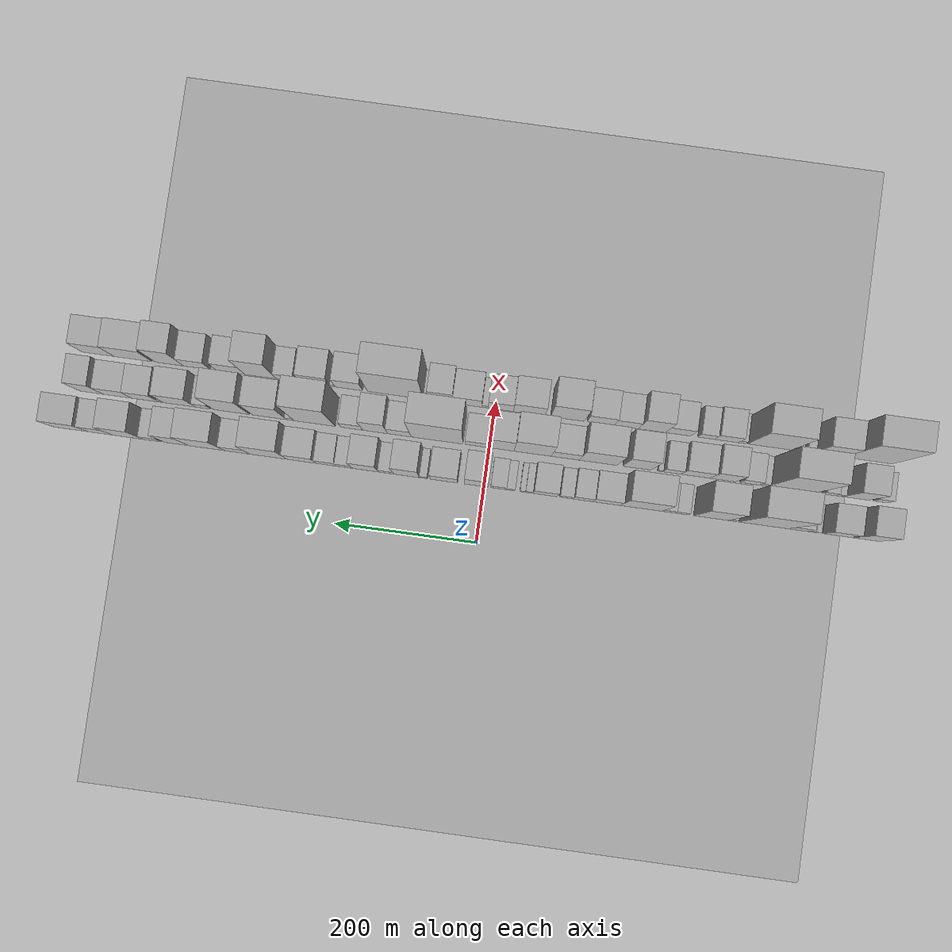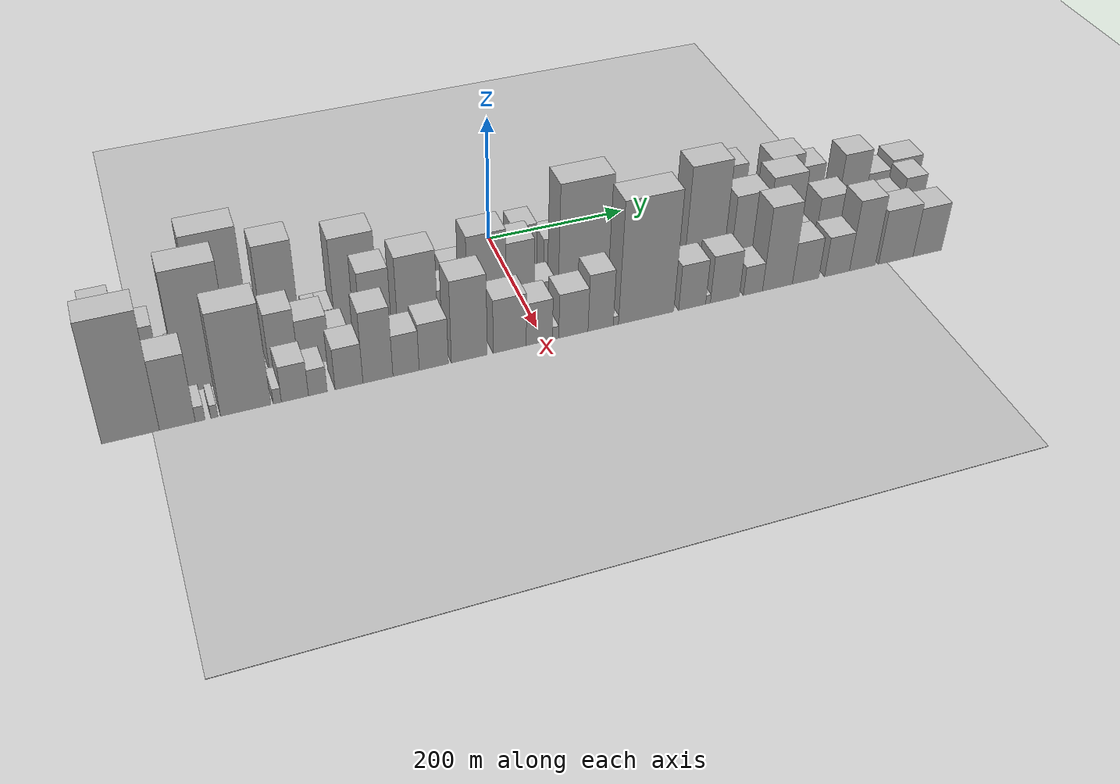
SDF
<?xml version="1.0" encoding="utf-8"?>

<sdf version="1.6">

   <world name="default">

      <gui fullscreen="0">

         <camera name="user_camera">

            <pose>-15 0 4.57585 0 0 0</pose>

            <view_controller>orbit</view_controller>

         </camera>

      </gui>

      <scene>

         <sky>

           <clouds>

             <speed>12</speed>

           </clouds>

         </sky>

         <ambient>0.4 0.4 0.4 1</ambient>

         <background>0.7 0.7 0.7 1</background>

         <shadows>1</shadows>

      </scene>

      <gravity>0 0 -9.8066</gravity>

      <magnetic_field>6e-06 2.3e-05 -4.2e-05</magnetic_field>

      <physics default="0" name="default_physics" type="ode">

         <ode>

            <solver>

               <type>quick</type>

               <iters>10</iters>

               <sor>1.0</sor>

               <use_dynamic_moi_rescaling>0</use_dynamic_moi_rescaling>

            </solver>

            <constraints>

               <cfm>0</cfm>

               <erp>0.2</erp>

               <contact_max_correcting_vel>100</contact_max_correcting_vel>

               <contact_surface_layer>0.001</contact_surface_layer>

            </constraints>

         </ode>

         <max_step_size>0.004</max_step_size>

         <real_time_factor>1</real_time_factor>

         <real_time_update_rate>250</real_time_update_rate>

      </physics>

      <light name="sun" type="directional">

         <cast_shadows>1</cast_shadows>

         <pose>0 0 10 0 0 0</pose>

         <diffuse>0.8 0.8 0.8 1</diffuse>

         <specular>0.2 0.2 0.2 1</specular>

         <attenuation>

            <range>1000</range>

            <constant>0.9</constant>

            <linear>0.01</linear>

            <quadratic>0.001</quadratic>

         </attenuation>

         <direction>-0.5 0.1 -0.9</direction>

      </light>

      <include>

         <name>ground_plane_1</name>

         <uri>model://HANNAS_ground_plane</uri>

         <pose>0 0 0  0 0 0</pose>

      </include>

      <include>

         <name>ground_plane_2</name>

         <uri>model://HANNAS_ground_plane</uri>

         <pose>100 0 0  0 0 0</pose>

      </include>

      <model name="building_1">

         <static>1</static>

         <pose frame="">100.0000 -535.5505 0 0.000000 0.000000 0.000000</pose>

         <link name="link">

            <pose frame="">0 0 58.50 0 0 0</pose>

            <collision name="collision">

               <geometry>

                  <box>

                     <size>40.0000 36.8990 117.0000</size>

                  </box>

               </geometry>

               <max_contacts>10</max_contacts>

               <surface>

                  <contact>

                     <ode/>

                  </contact>

                  <bounce/>

                  <friction>

                     <torsional>

                        <ode/>

                     </torsional>

                     <ode/>

                  </friction>

               </surface>

            </collision>

            <visual name="visual">

               <cast_shadows>0</cast_shadows>

               <geometry>

                  <box>

                     <size>40.0000 36.8990 117.0000</size>

                  </box>

               </geometry>

               <material>

                  <script>

                     <uri>model://HANNAS_wall/materials/scripts</uri>

                     <uri>model://HANNAS_wall/materials/textures</uri>

                     <name>vrc/HANNAS_wall</name>

                  </script>

               </material>

            </visual>

            <self_collide>0</self_collide>

            <enable_wind>0</enable_wind>

            <kinematic>0</kinematic>

         </link>

      </model>

      <model name="building_2">

         <static>1</static>

         <pose frame="">100.0000 -494.7667 0 0.000000 0.000000 0.000000</pose>

         <link name="link">

            <pose frame="">0 0 36.00 0 0 0</pose>

            <collision name="collision">

               <geometry>

                  <box>

                     <size>40.0000 38.6686 72.0000</size>

                  </box>

               </geometry>

               <max_contacts>10</max_contacts>

               <surface>

                  <contact>

                     <ode/>

                  </contact>

                  <bounce/>

                  <friction>

                     <torsional>

                        <ode/>

                     </torsional>

                     <ode/>

                  </friction>

               </surface>

            </collision>

            <visual name="visual">

               <cast_shadows>0</cast_shadows>

               <geometry>

                  <box>

                     <size>40.0000 38.6686 72.0000</size>

                  </box>

               </geometry>

               <material>

                  <script>

                     <uri>model://HANNAS_wall/materials/scripts</uri>

                     <uri>model://HANNAS_wall/materials/textures</uri>

                     <name>vrc/HANNAS_wall</name>

                  </script>

               </material>

            </visual>

            <self_collide>0</self_collide>

            <enable_wind>0</enable_wind>

            <kinematic>0</kinematic>

         </link>

      </model>

      <model name="building_3">

         <static>1</static>

         <pose frame="">100.0000 -466.4745 0 0.000000 0.000000 0.000000</pose>

         <link name="link">

            <pose frame="">0 0 9.00 0 0 0</pose>

            <collision name="collision">

               <geometry>

                  <box>

                     <size>40.0000 7.9157 18.0000</size>

                  </box>

               </geometry>

               <max_contacts>10</max_contacts>

               <surface>

                  <contact>

                     <ode/>

                  </contact>

                  <bounce/>

                  <friction>

                     <torsional>

                        <ode/>

                     </torsional>

                     <ode/>

                  </friction>

               </surface>

            </collision>

            <visual name="visual">

               <cast_shadows>0</cast_shadows>

               <geometry>

                  <box>

                     <size>40.0000 7.9157 18.0000</size>

                  </box>

               </geometry>

               <material>

                  <script>

                     <uri>model://HANNAS_wall/materials/scripts</uri>

                     <uri>model://HANNAS_wall/materials/textures</uri>

                     <name>vrc/HANNAS_wall</name>

                  </script>

               </material>

            </visual>

            <self_collide>0</self_collide>

            <enable_wind>0</enable_wind>

            <kinematic>0</kinematic>

         </link>

      </model>

      <model name="building_4">

         <static>1</static>

         <pose frame="">100.0000 -458.2818 0 0.000000 0.000000 0.000000</pose>

         <link name="link">

            <pose frame="">0 0 10.50 0 0 0</pose>

            <collision name="collision">

               <geometry>

                  <box>

                     <size>40.0000 8.4698 21.0000</size>

                  </box>

               </geometry>

               <max_contacts>10</max_contacts>

               <surface>

                  <contact>

                     <ode/>

                  </contact>

                  <bounce/>

                  <friction>

                     <torsional>

                        <ode/>

                     </torsional>

                     <ode/>

                  </friction>

               </surface>

            </collision>

            <visual name="visual">

               <cast_shadows>0</cast_shadows>

               <geometry>

                  <box>

                     <size>40.0000 8.4698 21.0000</size>

                  </box>

               </geometry>

               <material>

                  <script>

                     <uri>model://HANNAS_wall/materials/scripts</uri>

                     <uri>model://HANNAS_wall/materials/textures</uri>

                     <name>vrc/HANNAS_wall</name>

                  </script>

               </material>

            </visual>

            <self_collide>0</self_collide>

            <enable_wind>0</enable_wind>

            <kinematic>0</kinematic>

         </link>

      </model>

      <model name="building_5">

         <static>1</static>

         <pose frame="">100.0000 -440.0761 0 0.000000 0.000000 0.000000</pose>

         <link name="link">

            <pose frame="">0 0 27.00 0 0 0</pose>

            <collision name="collision">

               <geometry>

                  <box>

                     <size>40.0000 27.9417 54.0000</size>

                  </box>

               </geometry>

               <max_contacts>10</max_contacts>

               <surface>

                  <contact>

                     <ode/>

                  </contact>

                  <bounce/>

                  <friction>

                     <torsional>

                        <ode/>

                     </torsional>

                     <ode/>

                  </friction>

               </surface>

            </collision>

            <visual name="visual">

               <cast_shadows>0</cast_shadows>

               <geometry>

                  <box>

                     <size>40.0000 27.9417 54.0000</size>

                  </box>

               </geometry>

               <material>

                  <script>

                     <uri>model://HANNAS_wall/materials/scripts</uri>

                     <uri>model://HANNAS_wall/materials/textures</uri>

                     <name>vrc/HANNAS_wall</name>

                  </script>

               </material>

            </visual>

            <self_collide>0</self_collide>

            <enable_wind>0</enable_wind>

            <kinematic>0</kinematic>

         </link>

      </model>

      <model name="building_6">

         <static>1</static>

         <pose frame="">100.0000 -391.7738 0 0.000000 0.000000 0.000000</pose>

         <link name="link">

            <pose frame="">0 0 97.50 0 0 0</pose>

            <collision name="collision">

               <geometry>

                  <box>

                     <size>40.0000 68.6630 195.0000</size>

                  </box>

               </geometry>

               <max_contacts>10</max_contacts>

               <surface>

                  <contact>

                     <ode/>

                  </contact>

                  <bounce/>

                  <friction>

                     <torsional>

                        <ode/>

                     </torsional>

                     <ode/>

                  </friction>

               </surface>

            </collision>

            <visual name="visual">

               <cast_shadows>0</cast_shadows>

               <geometry>

                  <box>

                     <size>40.0000 68.6630 195.0000</size>

                  </box>

               </geometry>

               <material>

                  <script>

                     <uri>model://HANNAS_wall/materials/scripts</uri>

                     <uri>model://HANNAS_wall/materials/textures</uri>

                     <name>vrc/HANNAS_wall</name>

                  </script>

               </material>

            </visual>

            <self_collide>0</self_collide>

            <enable_wind>0</enable_wind>

            <kinematic>0</kinematic>

         </link>

      </model>

      <model name="building_7">

         <static>1</static>

         <pose frame="">100.0000 -347.8952 0 0.000000 0.000000 0.000000</pose>

         <link name="link">

            <pose frame="">0 0 13.50 0 0 0</pose>

            <collision name="collision">

               <geometry>

                  <box>

                     <size>40.0000 11.0942 27.0000</size>

                  </box>

               </geometry>

               <max_contacts>10</max_contacts>

               <surface>

                  <contact>

                     <ode/>

                  </contact>

                  <bounce/>

                  <friction>

                     <torsional>

                        <ode/>

                     </torsional>

                     <ode/>

                  </friction>

               </surface>

            </collision>

            <visual name="visual">

               <cast_shadows>0</cast_shadows>

               <geometry>

                  <box>

                     <size>40.0000 11.0942 27.0000</size>

                  </box>

               </geometry>

               <material>

                  <script>

                     <uri>model://HANNAS_wall/materials/scripts</uri>

                     <uri>model://HANNAS_wall/materials/textures</uri>

                     <name>vrc/HANNAS_wall</name>

                  </script>

               </material>

            </visual>

            <self_collide>0</self_collide>

            <enable_wind>0</enable_wind>

            <kinematic>0</kinematic>

         </link>

      </model>

      <model name="building_8">

         <static>1</static>

         <pose frame="">100.0000 -318.2536 0 0.000000 0.000000 0.000000</pose>

         <link name="link">

            <pose frame="">0 0 79.50 0 0 0</pose>

            <collision name="collision">

               <geometry>

                  <box>

                     <size>40.0000 48.1891 159.0000</size>

                  </box>

               </geometry>

               <max_contacts>10</max_contacts>

               <surface>

                  <contact>

                     <ode/>

                  </contact>

                  <bounce/>

                  <friction>

                     <torsional>

                        <ode/>

                     </torsional>

                     <ode/>

                  </friction>

               </surface>

            </collision>

            <visual name="visual">

               <cast_shadows>0</cast_shadows>

               <geometry>

                  <box>

                     <size>40.0000 48.1891 159.0000</size>

                  </box>

               </geometry>

               <material>

                  <script>

                     <uri>model://HANNAS_wall/materials/scripts</uri>

                     <uri>model://HANNAS_wall/materials/textures</uri>

                     <name>vrc/HANNAS_wall</name>

                  </script>

               </material>

            </visual>

            <self_collide>0</self_collide>

            <enable_wind>0</enable_wind>

            <kinematic>0</kinematic>

         </link>

      </model>

      <model name="building_9">

         <static>1</static>

         <pose frame="">100.0000 -276.0487 0 0.000000 0.000000 0.000000</pose>

         <link name="link">

            <pose frame="">0 0 18.00 0 0 0</pose>

            <collision name="collision">

               <geometry>

                  <box>

                     <size>40.0000 18.2208 36.0000</size>

                  </box>

               </geometry>

               <max_contacts>10</max_contacts>

               <surface>

                  <contact>

                     <ode/>

                  </contact>

                  <bounce/>

                  <friction>

                     <torsional>

                        <ode/>

                     </torsional>

                     <ode/>

                  </friction>

               </surface>

            </collision>

            <visual name="visual">

               <cast_shadows>0</cast_shadows>

               <geometry>

                  <box>

                     <size>40.0000 18.2208 36.0000</size>

                  </box>

               </geometry>

               <material>

                  <script>

                     <uri>model://HANNAS_wall/materials/scripts</uri>

                     <uri>model://HANNAS_wall/materials/textures</uri>

                     <name>vrc/HANNAS_wall</name>

                  </script>

               </material>

            </visual>

            <self_collide>0</self_collide>

            <enable_wind>0</enable_wind>

            <kinematic>0</kinematic>

         </link>

      </model>

      <model name="building_10">

         <static>1</static>

         <pose frame="">100.0000 -257.8880 0 0.000000 0.000000 0.000000</pose>

         <link name="link">

            <pose frame="">0 0 18.00 0 0 0</pose>

            <collision name="collision">

               <geometry>

                  <box>

                     <size>40.0000 18.1005 36.0000</size>

                  </box>

               </geometry>

               <max_contacts>10</max_contacts>

               <surface>

                  <contact>

                     <ode/>

                  </contact>

                  <bounce/>

                  <friction>

                     <torsional>

                        <ode/>

                     </torsional>

                     <ode/>

                  </friction>

               </surface>

            </collision>

            <visual name="visual">

               <cast_shadows>0</cast_shadows>

               <geometry>

                  <box>

                     <size>40.0000 18.1005 36.0000</size>

                  </box>

               </geometry>

               <material>

                  <script>

                     <uri>model://HANNAS_wall/materials/scripts</uri>

                     <uri>model://HANNAS_wall/materials/textures</uri>

                     <name>vrc/HANNAS_wall</name>

                  </script>

               </material>

            </visual>

            <self_collide>0</self_collide>

            <enable_wind>0</enable_wind>

            <kinematic>0</kinematic>

         </link>

      </model>

      <model name="building_11">

         <static>1</static>

         <pose frame="">100.0000 -219.7703 0 0.000000 0.000000 0.000000</pose>

         <link name="link">

            <pose frame="">0 0 73.50 0 0 0</pose>

            <collision name="collision">

               <geometry>

                  <box>

                     <size>40.0000 58.1349 147.0000</size>

                  </box>

               </geometry>

               <max_contacts>10</max_contacts>

               <surface>

                  <contact>

                     <ode/>

                  </contact>

                  <bounce/>

                  <friction>

                     <torsional>

                        <ode/>

                     </torsional>

                     <ode/>

                  </friction>

               </surface>

            </collision>

            <visual name="visual">

               <cast_shadows>0</cast_shadows>

               <geometry>

                  <box>

                     <size>40.0000 58.1349 147.0000</size>

                  </box>

               </geometry>

               <material>

                  <script>

                     <uri>model://HANNAS_wall/materials/scripts</uri>

                     <uri>model://HANNAS_wall/materials/textures</uri>

                     <name>vrc/HANNAS_wall</name>

                  </script>

               </material>

            </visual>

            <self_collide>0</self_collide>

            <enable_wind>0</enable_wind>

            <kinematic>0</kinematic>

         </link>

      </model>

      <model name="building_12">

         <static>1</static>

         <pose frame="">100.0000 -171.3917 0 0.000000 0.000000 0.000000</pose>

         <link name="link">

            <pose frame="">0 0 33.00 0 0 0</pose>

            <collision name="collision">

               <geometry>

                  <box>

                     <size>40.0000 38.6224 66.0000</size>

                  </box>

               </geometry>

               <max_contacts>10</max_contacts>

               <surface>

                  <contact>

                     <ode/>

                  </contact>

                  <bounce/>

                  <friction>

                     <torsional>

                        <ode/>

                     </torsional>

                     <ode/>

                  </friction>

               </surface>

            </collision>

            <visual name="visual">

               <cast_shadows>0</cast_shadows>

               <geometry>

                  <box>

                     <size>40.0000 38.6224 66.0000</size>

                  </box>

               </geometry>

               <material>

                  <script>

                     <uri>model://HANNAS_wall/materials/scripts</uri>

                     <uri>model://HANNAS_wall/materials/textures</uri>

                     <name>vrc/HANNAS_wall</name>

                  </script>

               </material>

            </visual>

            <self_collide>0</self_collide>

            <enable_wind>0</enable_wind>

            <kinematic>0</kinematic>

         </link>

      </model>

      <model name="building_13">

         <static>1</static>

         <pose frame="">100.0000 -138.2417 0 0.000000 0.000000 0.000000</pose>

         <link name="link">

            <pose frame="">0 0 27.00 0 0 0</pose>

            <collision name="collision">

               <geometry>

                  <box>

                     <size>40.0000 27.6775 54.0000</size>

                  </box>

               </geometry>

               <max_contacts>10</max_contacts>

               <surface>

                  <contact>

                     <ode/>

                  </contact>

                  <bounce/>

                  <friction>

                     <torsional>

                        <ode/>

                     </torsional>

                     <ode/>

                  </friction>

               </surface>

            </collision>

            <visual name="visual">

               <cast_shadows>0</cast_shadows>

               <geometry>

                  <box>

                     <size>40.0000 27.6775 54.0000</size>

                  </box>

               </geometry>

               <material>

                  <script>

                     <uri>model://HANNAS_wall/materials/scripts</uri>

                     <uri>model://HANNAS_wall/materials/textures</uri>

                     <name>vrc/HANNAS_wall</name>

                  </script>

               </material>

            </visual>

            <self_collide>0</self_collide>

            <enable_wind>0</enable_wind>

            <kinematic>0</kinematic>

         </link>

      </model>

      <model name="building_14">

         <static>1</static>

         <pose frame="">100.0000 -114.8564 0 0.000000 0.000000 0.000000</pose>

         <link name="link">

            <pose frame="">0 0 16.50 0 0 0</pose>

            <collision name="collision">

               <geometry>

                  <box>

                     <size>40.0000 19.0930 33.0000</size>

                  </box>

               </geometry>

               <max_contacts>10</max_contacts>

               <surface>

                  <contact>

                     <ode/>

                  </contact>

                  <bounce/>

                  <friction>

                     <torsional>

                        <ode/>

                     </torsional>

                     <ode/>

                  </friction>

               </surface>

            </collision>

            <visual name="visual">

               <cast_shadows>0</cast_shadows>

               <geometry>

                  <box>

                     <size>40.0000 19.0930 33.0000</size>

                  </box>

               </geometry>

               <material>

                  <script>

                     <uri>model://HANNAS_wall/materials/scripts</uri>

                     <uri>model://HANNAS_wall/materials/textures</uri>

                     <name>vrc/HANNAS_wall</name>

                  </script>

               </material>

            </visual>

            <self_collide>0</self_collide>

            <enable_wind>0</enable_wind>

            <kinematic>0</kinematic>

         </link>

      </model>

      <model name="building_15">

         <static>1</static>

         <pose frame="">100.0000 -85.0849 0 0.000000 0.000000 0.000000</pose>

         <link name="link">

            <pose frame="">0 0 31.50 0 0 0</pose>

            <collision name="collision">

               <geometry>

                  <box>

                     <size>40.0000 34.4501 63.0000</size>

                  </box>

               </geometry>

               <max_contacts>10</max_contacts>

               <surface>

                  <contact>

                     <ode/>

                  </contact>

                  <bounce/>

                  <friction>

                     <torsional>

                        <ode/>

                     </torsional>

                     <ode/>

                  </friction>

               </surface>

            </collision>

            <visual name="visual">

               <cast_shadows>0</cast_shadows>

               <geometry>

                  <box>

                     <size>40.0000 34.4501 63.0000</size>

                  </box>

               </geometry>

               <material>

                  <script>

                     <uri>model://HANNAS_wall/materials/scripts</uri>

                     <uri>model://HANNAS_wall/materials/textures</uri>

                     <name>vrc/HANNAS_wall</name>

                  </script>

               </material>

            </visual>

            <self_collide>0</self_collide>

            <enable_wind>0</enable_wind>

            <kinematic>0</kinematic>

         </link>

      </model>

      <model name="building_16">

         <static>1</static>

         <pose frame="">100.0000 -62.6137 0 0.000000 0.000000 0.000000</pose>

         <link name="link">

            <pose frame="">0 0 12.00 0 0 0</pose>

            <collision name="collision">

               <geometry>

                  <box>

                     <size>40.0000 10.4922 24.0000</size>

                  </box>

               </geometry>

               <max_contacts>10</max_contacts>

               <surface>

                  <contact>

                     <ode/>

                  </contact>

                  <bounce/>

                  <friction>

                     <torsional>

                        <ode/>

                     </torsional>

                     <ode/>

                  </friction>

               </surface>

            </collision>

            <visual name="visual">

               <cast_shadows>0</cast_shadows>

               <geometry>

                  <box>

                     <size>40.0000 10.4922 24.0000</size>

                  </box>

               </geometry>

               <material>

                  <script>

                     <uri>model://HANNAS_wall/materials/scripts</uri>

                     <uri>model://HANNAS_wall/materials/textures</uri>

                     <name>vrc/HANNAS_wall</name>

                  </script>

               </material>

            </visual>

            <self_collide>0</self_collide>

            <enable_wind>0</enable_wind>

            <kinematic>0</kinematic>

         </link>

      </model>

      <model name="building_17">

         <static>1</static>

         <pose frame="">100.0000 -53.4701 0 0.000000 0.000000 0.000000</pose>

         <link name="link">

            <pose frame="">0 0 9.00 0 0 0</pose>

            <collision name="collision">

               <geometry>

                  <box>

                     <size>40.0000 7.7951 18.0000</size>

                  </box>

               </geometry>

               <max_contacts>10</max_contacts>

               <surface>

                  <contact>

                     <ode/>

                  </contact>

                  <bounce/>

                  <friction>

                     <torsional>

                        <ode/>

                     </torsional>

                     <ode/>

                  </friction>

               </surface>

            </collision>

            <visual name="visual">

               <cast_shadows>0</cast_shadows>

               <geometry>

                  <box>

                     <size>40.0000 7.7951 18.0000</size>

                  </box>

               </geometry>

               <material>

                  <script>

                     <uri>model://HANNAS_wall/materials/scripts</uri>

                     <uri>model://HANNAS_wall/materials/textures</uri>

                     <name>vrc/HANNAS_wall</name>

                  </script>

               </material>

            </visual>

            <self_collide>0</self_collide>

            <enable_wind>0</enable_wind>

            <kinematic>0</kinematic>

         </link>

      </model>

      <model name="building_18">

         <static>1</static>

         <pose frame="">100.0000 -36.5034 0 0.000000 0.000000 0.000000</pose>

         <link name="link">

            <pose frame="">0 0 13.50 0 0 0</pose>

            <collision name="collision">

               <geometry>

                  <box>

                     <size>40.0000 12.1384 27.0000</size>

                  </box>

               </geometry>

               <max_contacts>10</max_contacts>

               <surface>

                  <contact>

                     <ode/>

                  </contact>

                  <bounce/>

                  <friction>

                     <torsional>

                        <ode/>

                     </torsional>

                     <ode/>

                  </friction>

               </surface>

            </collision>

            <visual name="visual">

               <cast_shadows>0</cast_shadows>

               <geometry>

                  <box>

                     <size>40.0000 12.1384 27.0000</size>

                  </box>

               </geometry>

               <material>

                  <script>

                     <uri>model://HANNAS_wall/materials/scripts</uri>

                     <uri>model://HANNAS_wall/materials/textures</uri>

                     <name>vrc/HANNAS_wall</name>

                  </script>

               </material>

            </visual>

            <self_collide>0</self_collide>

            <enable_wind>0</enable_wind>

            <kinematic>0</kinematic>

         </link>

      </model>

      <model name="building_19">

         <static>1</static>

         <pose frame="">100.0000 -19.3867 0 0.000000 0.000000 0.000000</pose>

         <link name="link">

            <pose frame="">0 0 19.50 0 0 0</pose>

            <collision name="collision">

               <geometry>

                  <box>

                     <size>40.0000 22.0950 39.0000</size>

                  </box>

               </geometry>

               <max_contacts>10</max_contacts>

               <surface>

                  <contact>

                     <ode/>

                  </contact>

                  <bounce/>

                  <friction>

                     <torsional>

                        <ode/>

                     </torsional>

                     <ode/>

                  </friction>

               </surface>

            </collision>

            <visual name="visual">

               <cast_shadows>0</cast_shadows>

               <geometry>

                  <box>

                     <size>40.0000 22.0950 39.0000</size>

                  </box>

               </geometry>

               <material>

                  <script>

                     <uri>model://HANNAS_wall/materials/scripts</uri>

                     <uri>model://HANNAS_wall/materials/textures</uri>

                     <name>vrc/HANNAS_wall</name>

                  </script>

               </material>

            </visual>

            <self_collide>0</self_collide>

            <enable_wind>0</enable_wind>

            <kinematic>0</kinematic>

         </link>

      </model>

      <model name="building_20">

         <static>1</static>

         <pose frame="">100.0000 11.2909 0 0.000000 0.000000 0.000000</pose>

         <link name="link">

            <pose frame="">0 0 52.50 0 0 0</pose>

            <collision name="collision">

               <geometry>

                  <box>

                     <size>40.0000 33.2602 105.0000</size>

                  </box>

               </geometry>

               <max_contacts>10</max_contacts>

               <surface>

                  <contact>

                     <ode/>

                  </contact>

                  <bounce/>

                  <friction>

                     <torsional>

                        <ode/>

                     </torsional>

                     <ode/>

                  </friction>

               </surface>

            </collision>

            <visual name="visual">

               <cast_shadows>0</cast_shadows>

               <geometry>

                  <box>

                     <size>40.0000 33.2602 105.0000</size>

                  </box>

               </geometry>

               <material>

                  <script>

                     <uri>model://HANNAS_wall/materials/scripts</uri>

                     <uri>model://HANNAS_wall/materials/textures</uri>

                     <name>vrc/HANNAS_wall</name>

                  </script>

               </material>

            </visual>

            <self_collide>0</self_collide>

            <enable_wind>0</enable_wind>

            <kinematic>0</kinematic>

         </link>

      </model>

      <model name="building_21">

         <static>1</static>

         <pose frame="">100.0000 57.2294 0 0.000000 0.000000 0.000000</pose>

         <link name="link">

            <pose frame="">0 0 37.50 0 0 0</pose>

            <collision name="collision">

               <geometry>

                  <box>

                     <size>40.0000 38.6168 75.0000</size>

                  </box>

               </geometry>

               <max_contacts>10</max_contacts>

               <surface>

                  <contact>

                     <ode/>

                  </contact>

                  <bounce/>

                  <friction>

                     <torsional>

                        <ode/>

                     </torsional>

                     <ode/>

                  </friction>

               </surface>

            </collision>

            <visual name="visual">

               <cast_shadows>0</cast_shadows>

               <geometry>

                  <box>

                     <size>40.0000 38.6168 75.0000</size>

                  </box>

               </geometry>

               <material>

                  <script>

                     <uri>model://HANNAS_wall/materials/scripts</uri>

                     <uri>model://HANNAS_wall/materials/textures</uri>

                     <name>vrc/HANNAS_wall</name>

                  </script>

               </material>

            </visual>

            <self_collide>0</self_collide>

            <enable_wind>0</enable_wind>

            <kinematic>0</kinematic>

         </link>

      </model>

      <model name="building_22">

         <static>1</static>

         <pose frame="">100.0000 85.9400 0 0.000000 0.000000 0.000000</pose>

         <link name="link">

            <pose frame="">0 0 13.50 0 0 0</pose>

            <collision name="collision">

               <geometry>

                  <box>

                     <size>40.0000 10.8043 27.0000</size>

                  </box>

               </geometry>

               <max_contacts>10</max_contacts>

               <surface>

                  <contact>

                     <ode/>

                  </contact>

                  <bounce/>

                  <friction>

                     <torsional>

                        <ode/>

                     </torsional>

                     <ode/>

                  </friction>

               </surface>

            </collision>

            <visual name="visual">

               <cast_shadows>0</cast_shadows>

               <geometry>

                  <box>

                     <size>40.0000 10.8043 27.0000</size>

                  </box>

               </geometry>

               <material>

                  <script>

                     <uri>model://HANNAS_wall/materials/scripts</uri>

                     <uri>model://HANNAS_wall/materials/textures</uri>

                     <name>vrc/HANNAS_wall</name>

                  </script>

               </material>

            </visual>

            <self_collide>0</self_collide>

            <enable_wind>0</enable_wind>

            <kinematic>0</kinematic>

         </link>

      </model>

      <model name="building_23">

         <static>1</static>

         <pose frame="">100.0000 109.5567 0 0.000000 0.000000 0.000000</pose>

         <link name="link">

            <pose frame="">0 0 57.00 0 0 0</pose>

            <collision name="collision">

               <geometry>

                  <box>

                     <size>40.0000 36.4291 114.0000</size>

                  </box>

               </geometry>

               <max_contacts>10</max_contacts>

               <surface>

                  <contact>

                     <ode/>

                  </contact>

                  <bounce/>

                  <friction>

                     <torsional>

                        <ode/>

                     </torsional>

                     <ode/>

                  </friction>

               </surface>

            </collision>

            <visual name="visual">

               <cast_shadows>0</cast_shadows>

               <geometry>

                  <box>

                     <size>40.0000 36.4291 114.0000</size>

                  </box>

               </geometry>

               <material>

                  <script>

                     <uri>model://HANNAS_wall/materials/scripts</uri>

                     <uri>model://HANNAS_wall/materials/textures</uri>

                     <name>vrc/HANNAS_wall</name>

                  </script>

               </material>

            </visual>

            <self_collide>0</self_collide>

            <enable_wind>0</enable_wind>

            <kinematic>0</kinematic>

         </link>

      </model>

      <model name="building_24">

         <static>1</static>

         <pose frame="">100.0000 138.3412 0 0.000000 0.000000 0.000000</pose>

         <link name="link">

            <pose frame="">0 0 18.00 0 0 0</pose>

            <collision name="collision">

               <geometry>

                  <box>

                     <size>40.0000 21.1399 36.0000</size>

                  </box>

               </geometry>

               <max_contacts>10</max_contacts>

               <surface>

                  <contact>

                     <ode/>

                  </contact>

                  <bounce/>

                  <friction>

                     <torsional>

                        <ode/>

                     </torsional>

                     <ode/>

                  </friction>

               </surface>

            </collision>

            <visual name="visual">

               <cast_shadows>0</cast_shadows>

               <geometry>

                  <box>

                     <size>40.0000 21.1399 36.0000</size>

                  </box>

               </geometry>

               <material>

                  <script>

                     <uri>model://HANNAS_wall/materials/scripts</uri>

                     <uri>model://HANNAS_wall/materials/textures</uri>

                     <name>vrc/HANNAS_wall</name>

                  </script>

               </material>

            </visual>

            <self_collide>0</self_collide>

            <enable_wind>0</enable_wind>

            <kinematic>0</kinematic>

         </link>

      </model>

      <model name="building_25">

         <static>1</static>

         <pose frame="">100.0000 167.5153 0 0.000000 0.000000 0.000000</pose>

         <link name="link">

            <pose frame="">0 0 49.50 0 0 0</pose>

            <collision name="collision">

               <geometry>

                  <box>

                     <size>40.0000 37.2082 99.0000</size>

                  </box>

               </geometry>

               <max_contacts>10</max_contacts>

               <surface>

                  <contact>

                     <ode/>

                  </contact>

                  <bounce/>

                  <friction>

                     <torsional>

                        <ode/>

                     </torsional>

                     <ode/>

                  </friction>

               </surface>

            </collision>

            <visual name="visual">

               <cast_shadows>0</cast_shadows>

               <geometry>

                  <box>

                     <size>40.0000 37.2082 99.0000</size>

                  </box>

               </geometry>

               <material>

                  <script>

                     <uri>model://HANNAS_wall/materials/scripts</uri>

                     <uri>model://HANNAS_wall/materials/textures</uri>

                     <name>vrc/HANNAS_wall</name>

                  </script>

               </material>

            </visual>

            <self_collide>0</self_collide>

            <enable_wind>0</enable_wind>

            <kinematic>0</kinematic>

         </link>

      </model>

      <model name="building_26">

         <static>1</static>

         <pose frame="">100.0000 197.5822 0 0.000000 0.000000 0.000000</pose>

         <link name="link">

            <pose frame="">0 0 19.50 0 0 0</pose>

            <collision name="collision">

               <geometry>

                  <box>

                     <size>40.0000 22.9257 39.0000</size>

                  </box>

               </geometry>

               <max_contacts>10</max_contacts>

               <surface>

                  <contact>

                     <ode/>

                  </contact>

                  <bounce/>

                  <friction>

                     <torsional>

                        <ode/>

                     </torsional>

                     <ode/>

                  </friction>

               </surface>

            </collision>

            <visual name="visual">

               <cast_shadows>0</cast_shadows>

               <geometry>

                  <box>

                     <size>40.0000 22.9257 39.0000</size>

                  </box>

               </geometry>

               <material>

                  <script>

                     <uri>model://HANNAS_wall/materials/scripts</uri>

                     <uri>model://HANNAS_wall/materials/textures</uri>

                     <name>vrc/HANNAS_wall</name>

                  </script>

               </material>

            </visual>

            <self_collide>0</self_collide>

            <enable_wind>0</enable_wind>

            <kinematic>0</kinematic>

         </link>

      </model>

      <model name="building_27">

         <static>1</static>

         <pose frame="">100.0000 223.0981 0 0.000000 0.000000 0.000000</pose>

         <link name="link">

            <pose frame="">0 0 24.00 0 0 0</pose>

            <collision name="collision">

               <geometry>

                  <box>

                     <size>40.0000 28.1060 48.0000</size>

                  </box>

               </geometry>

               <max_contacts>10</max_contacts>

               <surface>

                  <contact>

                     <ode/>

                  </contact>

                  <bounce/>

                  <friction>

                     <torsional>

                        <ode/>

                     </torsional>

                     <ode/>

                  </friction>

               </surface>

            </collision>

            <visual name="visual">

               <cast_shadows>0</cast_shadows>

               <geometry>

                  <box>

                     <size>40.0000 28.1060 48.0000</size>

                  </box>

               </geometry>

               <material>

                  <script>

                     <uri>model://HANNAS_wall/materials/scripts</uri>

                     <uri>model://HANNAS_wall/materials/textures</uri>

                     <name>vrc/HANNAS_wall</name>

                  </script>

               </material>

            </visual>

            <self_collide>0</self_collide>

            <enable_wind>0</enable_wind>

            <kinematic>0</kinematic>

         </link>

      </model>

      <model name="building_28">

         <static>1</static>

         <pose frame="">100.0000 257.6946 0 0.000000 0.000000 0.000000</pose>

         <link name="link">

            <pose frame="">0 0 37.50 0 0 0</pose>

            <collision name="collision">

               <geometry>

                  <box>

                     <size>40.0000 41.0869 75.0000</size>

                  </box>

               </geometry>

               <max_contacts>10</max_contacts>

               <surface>

                  <contact>

                     <ode/>

                  </contact>

                  <bounce/>

                  <friction>

                     <torsional>

                        <ode/>

                     </torsional>

                     <ode/>

                  </friction>

               </surface>

            </collision>

            <visual name="visual">

               <cast_shadows>0</cast_shadows>

               <geometry>

                  <box>

                     <size>40.0000 41.0869 75.0000</size>

                  </box>

               </geometry>

               <material>

                  <script>

                     <uri>model://HANNAS_wall/materials/scripts</uri>

                     <uri>model://HANNAS_wall/materials/textures</uri>

                     <name>vrc/HANNAS_wall</name>

                  </script>

               </material>

            </visual>

            <self_collide>0</self_collide>

            <enable_wind>0</enable_wind>

            <kinematic>0</kinematic>

         </link>

      </model>

      <model name="building_29">

         <static>1</static>

         <pose frame="">100.0000 304.1886 0 0.000000 0.000000 0.000000</pose>

         <link name="link">

            <pose frame="">0 0 66.00 0 0 0</pose>

            <collision name="collision">

               <geometry>

                  <box>

                     <size>40.0000 51.9012 132.0000</size>

                  </box>

               </geometry>

               <max_contacts>10</max_contacts>

               <surface>

                  <contact>

                     <ode/>

                  </contact>

                  <bounce/>

                  <friction>

                     <torsional>

                        <ode/>

                     </torsional>

                     <ode/>

                  </friction>

               </surface>

            </collision>

            <visual name="visual">

               <cast_shadows>0</cast_shadows>

               <geometry>

                  <box>

                     <size>40.0000 51.9012 132.0000</size>

                  </box>

               </geometry>

               <material>

                  <script>

                     <uri>model://HANNAS_wall/materials/scripts</uri>

                     <uri>model://HANNAS_wall/materials/textures</uri>

                     <name>vrc/HANNAS_wall</name>

                  </script>

               </material>

            </visual>

            <self_collide>0</self_collide>

            <enable_wind>0</enable_wind>

            <kinematic>0</kinematic>

         </link>

      </model>

      <model name="building_30">

         <static>1</static>

         <pose frame="">100.0000 348.5221 0 0.000000 0.000000 0.000000</pose>

         <link name="link">

            <pose frame="">0 0 31.50 0 0 0</pose>

            <collision name="collision">

               <geometry>

                  <box>

                     <size>40.0000 36.7659 63.0000</size>

                  </box>

               </geometry>

               <max_contacts>10</max_contacts>

               <surface>

                  <contact>

                     <ode/>

                  </contact>

                  <bounce/>

                  <friction>

                     <torsional>

                        <ode/>

                     </torsional>

                     <ode/>

                  </friction>

               </surface>

            </collision>

            <visual name="visual">

               <cast_shadows>0</cast_shadows>

               <geometry>

                  <box>

                     <size>40.0000 36.7659 63.0000</size>

                  </box>

               </geometry>

               <material>

                  <script>

                     <uri>model://HANNAS_wall/materials/scripts</uri>

                     <uri>model://HANNAS_wall/materials/textures</uri>

                     <name>vrc/HANNAS_wall</name>

                  </script>

               </material>

            </visual>

            <self_collide>0</self_collide>

            <enable_wind>0</enable_wind>

            <kinematic>0</kinematic>

         </link>

      </model>

      <model name="building_31">

         <static>1</static>

         <pose frame="">100.0000 391.8093 0 0.000000 0.000000 0.000000</pose>

         <link name="link">

            <pose frame="">0 0 64.50 0 0 0</pose>

            <collision name="collision">

               <geometry>

                  <box>

                     <size>40.0000 49.8083 129.0000</size>

                  </box>

               </geometry>

               <max_contacts>10</max_contacts>

               <surface>

                  <contact>

                     <ode/>

                  </contact>

                  <bounce/>

                  <friction>

                     <torsional>

                        <ode/>

                     </torsional>

                     <ode/>

                  </friction>

               </surface>

            </collision>

            <visual name="visual">

               <cast_shadows>0</cast_shadows>

               <geometry>

                  <box>

                     <size>40.0000 49.8083 129.0000</size>

                  </box>

               </geometry>

               <material>

                  <script>

                     <uri>model://HANNAS_wall/materials/scripts</uri>

                     <uri>model://HANNAS_wall/materials/textures</uri>

                     <name>vrc/HANNAS_wall</name>

                  </script>

               </material>

            </visual>

            <self_collide>0</self_collide>

            <enable_wind>0</enable_wind>

            <kinematic>0</kinematic>

         </link>

      </model>

      <model name="building_32">

         <static>1</static>

         <pose frame="">100.0000 434.0224 0 0.000000 0.000000 0.000000</pose>

         <link name="link">

            <pose frame="">0 0 52.50 0 0 0</pose>

            <collision name="collision">

               <geometry>

                  <box>

                     <size>40.0000 34.6179 105.0000</size>

                  </box>

               </geometry>

               <max_contacts>10</max_contacts>

               <surface>

                  <contact>

                     <ode/>

                  </contact>

                  <bounce/>

                  <friction>

                     <torsional>

                        <ode/>

                     </torsional>

                     <ode/>

                  </friction>

               </surface>

            </collision>

            <visual name="visual">

               <cast_shadows>0</cast_shadows>

               <geometry>

                  <box>

                     <size>40.0000 34.6179 105.0000</size>

                  </box>

               </geometry>

               <material>

                  <script>

                     <uri>model://HANNAS_wall/materials/scripts</uri>

                     <uri>model://HANNAS_wall/materials/textures</uri>

                     <name>vrc/HANNAS_wall</name>

                  </script>

               </material>

            </visual>

            <self_collide>0</self_collide>

            <enable_wind>0</enable_wind>

            <kinematic>0</kinematic>

         </link>

      </model>

      <model name="building_33">

         <static>1</static>

         <pose frame="">100.0000 468.6477 0 0.000000 0.000000 0.000000</pose>

         <link name="link">

            <pose frame="">0 0 21.00 0 0 0</pose>

            <collision name="collision">

               <geometry>

                  <box>

                     <size>40.0000 24.6328 42.0000</size>

                  </box>

               </geometry>

               <max_contacts>10</max_contacts>

               <surface>

                  <contact>

                     <ode/>

                  </contact>

                  <bounce/>

                  <friction>

                     <torsional>

                        <ode/>

                     </torsional>

                     <ode/>

                  </friction>

               </surface>

            </collision>

            <visual name="visual">

               <cast_shadows>0</cast_shadows>

               <geometry>

                  <box>

                     <size>40.0000 24.6328 42.0000</size>

                  </box>

               </geometry>

               <material>

                  <script>

                     <uri>model://HANNAS_wall/materials/scripts</uri>

                     <uri>model://HANNAS_wall/materials/textures</uri>

                     <name>vrc/HANNAS_wall</name>

                  </script>

               </material>

            </visual>

            <self_collide>0</self_collide>

            <enable_wind>0</enable_wind>

            <kinematic>0</kinematic>

         </link>

      </model>

      <model name="building_34">

         <static>1</static>

         <pose frame="">100.0000 502.6056 0 0.000000 0.000000 0.000000</pose>

         <link name="link">

            <pose frame="">0 0 55.50 0 0 0</pose>

            <collision name="collision">

               <geometry>

                  <box>

                     <size>40.0000 43.2830 111.0000</size>

                  </box>

               </geometry>

               <max_contacts>10</max_contacts>

               <surface>

                  <contact>

                     <ode/>

                  </contact>

                  <bounce/>

                  <friction>

                     <torsional>

                        <ode/>

                     </torsional>

                     <ode/>

                  </friction>

               </surface>

            </collision>

            <visual name="visual">

               <cast_shadows>0</cast_shadows>

               <geometry>

                  <box>

                     <size>40.0000 43.2830 111.0000</size>

                  </box>

               </geometry>

               <material>

                  <script>

                     <uri>model://HANNAS_wall/materials/scripts</uri>

                     <uri>model://HANNAS_wall/materials/textures</uri>

                     <name>vrc/HANNAS_wall</name>

                  </script>

               </material>

            </visual>

            <self_collide>0</self_collide>

            <enable_wind>0</enable_wind>

            <kinematic>0</kinematic>

         </link>

      </model>

      <model name="building_35">

         <static>1</static>

         <pose frame="">100.0000 542.0786 0 0.000000 0.000000 0.000000</pose>

         <link name="link">

            <pose frame="">0 0 34.50 0 0 0</pose>

            <collision name="collision">

               <geometry>

                  <box>

                     <size>40.0000 35.6630 69.0000</size>

                  </box>

               </geometry>

               <max_contacts>10</max_contacts>

               <surface>

                  <contact>

                     <ode/>

                  </contact>

                  <bounce/>

                  <friction>

                     <torsional>

                        <ode/>

                     </torsional>

                     <ode/>

                  </friction>

               </surface>

            </collision>

            <visual name="visual">

               <cast_shadows>0</cast_shadows>

               <geometry>

                  <box>

                     <size>40.0000 35.6630 69.0000</size>

                  </box>

               </geometry>

               <material>

                  <script>

                     <uri>model://HANNAS_wall/materials/scripts</uri>

                     <uri>model://HANNAS_wall/materials/textures</uri>

                     <name>vrc/HANNAS_wall</name>

                  </script>

               </material>

            </visual>

            <self_collide>0</self_collide>

            <enable_wind>0</enable_wind>

            <kinematic>0</kinematic>

         </link>

      </model>

      <model name="building_36">

         <static>1</static>

         <pose frame="">100.0000 584.0762 0 0.000000 0.000000 0.000000</pose>

         <link name="link">

            <pose frame="">0 0 42.00 0 0 0</pose>

            <collision name="collision">

               <geometry>

                  <box>

                     <size>40.0000 48.3321 84.0000</size>

                  </box>

               </geometry>

               <max_contacts>10</max_contacts>

               <surface>

                  <contact>

                     <ode/>

                  </contact>

                  <bounce/>

                  <friction>

                     <torsional>

                        <ode/>

                     </torsional>

                     <ode/>

                  </friction>

               </surface>

            </collision>

            <visual name="visual">

               <cast_shadows>0</cast_shadows>

               <geometry>

                  <box>

                     <size>40.0000 48.3321 84.0000</size>

                  </box>

               </geometry>

               <material>

                  <script>

                     <uri>model://HANNAS_wall/materials/scripts</uri>

                     <uri>model://HANNAS_wall/materials/textures</uri>

                     <name>vrc/HANNAS_wall</name>

                  </script>

               </material>

            </visual>

            <self_collide>0</self_collide>

            <enable_wind>0</enable_wind>

            <kinematic>0</kinematic>

         </link>

      </model>

      <model name="building_37">

         <static>1</static>

         <pose frame="">155.0000 -549.6959 0 0.000000 0.000000 0.000000</pose>

         <link name="link">

            <pose frame="">0 0 19.50 0 0 0</pose>

            <collision name="collision">

               <geometry>

                  <box>

                     <size>40.0000 20.6082 39.0000</size>

                  </box>

               </geometry>

               <max_contacts>10</max_contacts>

               <surface>

                  <contact>

                     <ode/>

                  </contact>

                  <bounce/>

                  <friction>

                     <torsional>

                        <ode/>

                     </torsional>

                     <ode/>

                  </friction>

               </surface>

            </collision>

            <visual name="visual">

               <cast_shadows>0</cast_shadows>

               <geometry>

                  <box>

                     <size>40.0000 20.6082 39.0000</size>

                  </box>

               </geometry>

               <material>

                  <script>

                     <uri>model://HANNAS_wall/materials/scripts</uri>

                     <uri>model://HANNAS_wall/materials/textures</uri>

                     <name>vrc/HANNAS_wall</name>

                  </script>

               </material>

            </visual>

            <self_collide>0</self_collide>

            <enable_wind>0</enable_wind>

            <kinematic>0</kinematic>

         </link>

      </model>

      <model name="building_38">

         <static>1</static>

         <pose frame="">155.0000 -515.3223 0 0.000000 0.000000 0.000000</pose>

         <link name="link">

            <pose frame="">0 0 54.00 0 0 0</pose>

            <collision name="collision">

               <geometry>

                  <box>

                     <size>40.0000 36.1389 108.0000</size>

                  </box>

               </geometry>

               <max_contacts>10</max_contacts>

               <surface>

                  <contact>

                     <ode/>

                  </contact>

                  <bounce/>

                  <friction>

                     <torsional>

                        <ode/>

                     </torsional>

                     <ode/>

                  </friction>

               </surface>

            </collision>

            <visual name="visual">

               <cast_shadows>0</cast_shadows>

               <geometry>

                  <box>

                     <size>40.0000 36.1389 108.0000</size>

                  </box>

               </geometry>

               <material>

                  <script>

                     <uri>model://HANNAS_wall/materials/scripts</uri>

                     <uri>model://HANNAS_wall/materials/textures</uri>

                     <name>vrc/HANNAS_wall</name>

                  </script>

               </material>

            </visual>

            <self_collide>0</self_collide>

            <enable_wind>0</enable_wind>

            <kinematic>0</kinematic>

         </link>

      </model>

      <model name="building_39">

         <static>1</static>

         <pose frame="">155.0000 -491.7513 0 0.000000 0.000000 0.000000</pose>

         <link name="link">

            <pose frame="">0 0 12.00 0 0 0</pose>

            <collision name="collision">

               <geometry>

                  <box>

                     <size>40.0000 11.0030 24.0000</size>

                  </box>

               </geometry>

               <max_contacts>10</max_contacts>

               <surface>

                  <contact>

                     <ode/>

                  </contact>

                  <bounce/>

                  <friction>

                     <torsional>

                        <ode/>

                     </torsional>

                     <ode/>

                  </friction>

               </surface>

            </collision>

            <visual name="visual">

               <cast_shadows>0</cast_shadows>

               <geometry>

                  <box>

                     <size>40.0000 11.0030 24.0000</size>

                  </box>

               </geometry>

               <material>

                  <script>

                     <uri>model://HANNAS_wall/materials/scripts</uri>

                     <uri>model://HANNAS_wall/materials/textures</uri>

                     <name>vrc/HANNAS_wall</name>

                  </script>

               </material>

            </visual>

            <self_collide>0</self_collide>

            <enable_wind>0</enable_wind>

            <kinematic>0</kinematic>

         </link>

      </model>

      <model name="building_40">

         <static>1</static>

         <pose frame="">155.0000 -476.9109 0 0.000000 0.000000 0.000000</pose>

         <link name="link">

            <pose frame="">0 0 16.50 0 0 0</pose>

            <collision name="collision">

               <geometry>

                  <box>

                     <size>40.0000 18.6778 33.0000</size>

                  </box>

               </geometry>

               <max_contacts>10</max_contacts>

               <surface>

                  <contact>

                     <ode/>

                  </contact>

                  <bounce/>

                  <friction>

                     <torsional>

                        <ode/>

                     </torsional>

                     <ode/>

                  </friction>

               </surface>

            </collision>

            <visual name="visual">

               <cast_shadows>0</cast_shadows>

               <geometry>

                  <box>

                     <size>40.0000 18.6778 33.0000</size>

                  </box>

               </geometry>

               <material>

                  <script>

                     <uri>model://HANNAS_wall/materials/scripts</uri>

                     <uri>model://HANNAS_wall/materials/textures</uri>

                     <name>vrc/HANNAS_wall</name>

                  </script>

               </material>

            </visual>

            <self_collide>0</self_collide>

            <enable_wind>0</enable_wind>

            <kinematic>0</kinematic>

         </link>

      </model>

      <model name="building_41">

         <static>1</static>

         <pose frame="">155.0000 -424.9604 0 0.000000 0.000000 0.000000</pose>

         <link name="link">

            <pose frame="">0 0 96.00 0 0 0</pose>

            <collision name="collision">

               <geometry>

                  <box>

                     <size>40.0000 67.2231 192.0000</size>

                  </box>

               </geometry>

               <max_contacts>10</max_contacts>

               <surface>

                  <contact>

                     <ode/>

                  </contact>

                  <bounce/>

                  <friction>

                     <torsional>

                        <ode/>

                     </torsional>

                     <ode/>

                  </friction>

               </surface>

            </collision>

            <visual name="visual">

               <cast_shadows>0</cast_shadows>

               <geometry>

                  <box>

                     <size>40.0000 67.2231 192.0000</size>

                  </box>

               </geometry>

               <material>

                  <script>

                     <uri>model://HANNAS_wall/materials/scripts</uri>

                     <uri>model://HANNAS_wall/materials/textures</uri>

                     <name>vrc/HANNAS_wall</name>

                  </script>

               </material>

            </visual>

            <self_collide>0</self_collide>

            <enable_wind>0</enable_wind>

            <kinematic>0</kinematic>

         </link>

      </model>

      <model name="building_42">

         <static>1</static>

         <pose frame="">155.0000 -385.1806 0 0.000000 0.000000 0.000000</pose>

         <link name="link">

            <pose frame="">0 0 13.50 0 0 0</pose>

            <collision name="collision">

               <geometry>

                  <box>

                     <size>40.0000 12.3365 27.0000</size>

                  </box>

               </geometry>

               <max_contacts>10</max_contacts>

               <surface>

                  <contact>

                     <ode/>

                  </contact>

                  <bounce/>

                  <friction>

                     <torsional>

                        <ode/>

                     </torsional>

                     <ode/>

                  </friction>

               </surface>

            </collision>

            <visual name="visual">

               <cast_shadows>0</cast_shadows>

               <geometry>

                  <box>

                     <size>40.0000 12.3365 27.0000</size>

                  </box>

               </geometry>

               <material>

                  <script>

                     <uri>model://HANNAS_wall/materials/scripts</uri>

                     <uri>model://HANNAS_wall/materials/textures</uri>

                     <name>vrc/HANNAS_wall</name>

                  </script>

               </material>

            </visual>

            <self_collide>0</self_collide>

            <enable_wind>0</enable_wind>

            <kinematic>0</kinematic>

         </link>

      </model>

      <model name="building_43">

         <static>1</static>

         <pose frame="">155.0000 -365.5989 0 0.000000 0.000000 0.000000</pose>

         <link name="link">

            <pose frame="">0 0 24.00 0 0 0</pose>

            <collision name="collision">

               <geometry>

                  <box>

                     <size>40.0000 26.8269 48.0000</size>

                  </box>

               </geometry>

               <max_contacts>10</max_contacts>

               <surface>

                  <contact>

                     <ode/>

                  </contact>

                  <bounce/>

                  <friction>

                     <torsional>

                        <ode/>

                     </torsional>

                     <ode/>

                  </friction>

               </surface>

            </collision>

            <visual name="visual">

               <cast_shadows>0</cast_shadows>

               <geometry>

                  <box>

                     <size>40.0000 26.8269 48.0000</size>

                  </box>

               </geometry>

               <material>

                  <script>

                     <uri>model://HANNAS_wall/materials/scripts</uri>

                     <uri>model://HANNAS_wall/materials/textures</uri>

                     <name>vrc/HANNAS_wall</name>

                  </script>

               </material>

            </visual>

            <self_collide>0</self_collide>

            <enable_wind>0</enable_wind>

            <kinematic>0</kinematic>

         </link>

      </model>

      <model name="building_44">

         <static>1</static>

         <pose frame="">155.0000 -327.8745 0 0.000000 0.000000 0.000000</pose>

         <link name="link">

            <pose frame="">0 0 48.00 0 0 0</pose>

            <collision name="collision">

               <geometry>

                  <box>

                     <size>40.0000 36.6219 96.0000</size>

                  </box>

               </geometry>

               <max_contacts>10</max_contacts>

               <surface>

                  <contact>

                     <ode/>

                  </contact>

                  <bounce/>

                  <friction>

                     <torsional>

                        <ode/>

                     </torsional>

                     <ode/>

                  </friction>

               </surface>

            </collision>

            <visual name="visual">

               <cast_shadows>0</cast_shadows>

               <geometry>

                  <box>

                     <size>40.0000 36.6219 96.0000</size>

                  </box>

               </geometry>

               <material>

                  <script>

                     <uri>model://HANNAS_wall/materials/scripts</uri>

                     <uri>model://HANNAS_wall/materials/textures</uri>

                     <name>vrc/HANNAS_wall</name>

                  </script>

               </material>

            </visual>

            <self_collide>0</self_collide>

            <enable_wind>0</enable_wind>

            <kinematic>0</kinematic>

         </link>

      </model>

      <model name="building_45">

         <static>1</static>

         <pose frame="">155.0000 -289.3366 0 0.000000 0.000000 0.000000</pose>

         <link name="link">

            <pose frame="">0 0 37.50 0 0 0</pose>

            <collision name="collision">

               <geometry>

                  <box>

                     <size>40.0000 40.4539 75.0000</size>

                  </box>

               </geometry>

               <max_contacts>10</max_contacts>

               <surface>

                  <contact>

                     <ode/>

                  </contact>

                  <bounce/>

                  <friction>

                     <torsional>

                        <ode/>

                     </torsional>

                     <ode/>

                  </friction>

               </surface>

            </collision>

            <visual name="visual">

               <cast_shadows>0</cast_shadows>

               <geometry>

                  <box>

                     <size>40.0000 40.4539 75.0000</size>

                  </box>

               </geometry>

               <material>

                  <script>

                     <uri>model://HANNAS_wall/materials/scripts</uri>

                     <uri>model://HANNAS_wall/materials/textures</uri>

                     <name>vrc/HANNAS_wall</name>

                  </script>

               </material>

            </visual>

            <self_collide>0</self_collide>

            <enable_wind>0</enable_wind>

            <kinematic>0</kinematic>

         </link>

      </model>

      <model name="building_46">

         <static>1</static>

         <pose frame="">155.0000 -256.2113 0 0.000000 0.000000 0.000000</pose>

         <link name="link">

            <pose frame="">0 0 24.00 0 0 0</pose>

            <collision name="collision">

               <geometry>

                  <box>

                     <size>40.0000 25.7966 48.0000</size>

                  </box>

               </geometry>

               <max_contacts>10</max_contacts>

               <surface>

                  <contact>

                     <ode/>

                  </contact>

                  <bounce/>

                  <friction>

                     <torsional>

                        <ode/>

                     </torsional>

                     <ode/>

                  </friction>

               </surface>

            </collision>

            <visual name="visual">

               <cast_shadows>0</cast_shadows>

               <geometry>

                  <box>

                     <size>40.0000 25.7966 48.0000</size>

                  </box>

               </geometry>

               <material>

                  <script>

                     <uri>model://HANNAS_wall/materials/scripts</uri>

                     <uri>model://HANNAS_wall/materials/textures</uri>

                     <name>vrc/HANNAS_wall</name>

                  </script>

               </material>

            </visual>

            <self_collide>0</self_collide>

            <enable_wind>0</enable_wind>

            <kinematic>0</kinematic>

         </link>

      </model>

      <model name="building_47">

         <static>1</static>

         <pose frame="">155.0000 -239.7607 0 0.000000 0.000000 0.000000</pose>

         <link name="link">

            <pose frame="">0 0 7.50 0 0 0</pose>

            <collision name="collision">

               <geometry>

                  <box>

                     <size>40.0000 7.1046 15.0000</size>

                  </box>

               </geometry>

               <max_contacts>10</max_contacts>

               <surface>

                  <contact>

                     <ode/>

                  </contact>

                  <bounce/>

                  <friction>

                     <torsional>

                        <ode/>

                     </torsional>

                     <ode/>

                  </friction>

               </surface>

            </collision>

            <visual name="visual">

               <cast_shadows>0</cast_shadows>

               <geometry>

                  <box>

                     <size>40.0000 7.1046 15.0000</size>

                  </box>

               </geometry>

               <material>

                  <script>

                     <uri>model://HANNAS_wall/materials/scripts</uri>

                     <uri>model://HANNAS_wall/materials/textures</uri>

                     <name>vrc/HANNAS_wall</name>

                  </script>

               </material>

            </visual>

            <self_collide>0</self_collide>

            <enable_wind>0</enable_wind>

            <kinematic>0</kinematic>

         </link>

      </model>

      <model name="building_48">

         <static>1</static>

         <pose frame="">155.0000 -207.1882 0 0.000000 0.000000 0.000000</pose>

         <link name="link">

            <pose frame="">0 0 64.50 0 0 0</pose>

            <collision name="collision">

               <geometry>

                  <box>

                     <size>40.0000 40.0405 129.0000</size>

                  </box>

               </geometry>

               <max_contacts>10</max_contacts>

               <surface>

                  <contact>

                     <ode/>

                  </contact>

                  <bounce/>

                  <friction>

                     <torsional>

                        <ode/>

                     </torsional>

                     <ode/>

                  </friction>

               </surface>

            </collision>

            <visual name="visual">

               <cast_shadows>0</cast_shadows>

               <geometry>

                  <box>

                     <size>40.0000 40.0405 129.0000</size>

                  </box>

               </geometry>

               <material>

                  <script>

                     <uri>model://HANNAS_wall/materials/scripts</uri>

                     <uri>model://HANNAS_wall/materials/textures</uri>

                     <name>vrc/HANNAS_wall</name>

                  </script>

               </material>

            </visual>

            <self_collide>0</self_collide>

            <enable_wind>0</enable_wind>

            <kinematic>0</kinematic>

         </link>

      </model>

      <model name="building_49">

         <static>1</static>

         <pose frame="">155.0000 -152.7702 0 0.000000 0.000000 0.000000</pose>

         <link name="link">

            <pose frame="">0 0 70.50 0 0 0</pose>

            <collision name="collision">

               <geometry>

                  <box>

                     <size>40.0000 52.7954 141.0000</size>

                  </box>

               </geometry>

               <max_contacts>10</max_contacts>

               <surface>

                  <contact>

                     <ode/>

                  </contact>

                  <bounce/>

                  <friction>

                     <torsional>

                        <ode/>

                     </torsional>

                     <ode/>

                  </friction>

               </surface>

            </collision>

            <visual name="visual">

               <cast_shadows>0</cast_shadows>

               <geometry>

                  <box>

                     <size>40.0000 52.7954 141.0000</size>

                  </box>

               </geometry>

               <material>

                  <script>

                     <uri>model://HANNAS_wall/materials/scripts</uri>

                     <uri>model://HANNAS_wall/materials/textures</uri>

                     <name>vrc/HANNAS_wall</name>

                  </script>

               </material>

            </visual>

            <self_collide>0</self_collide>

            <enable_wind>0</enable_wind>

            <kinematic>0</kinematic>

         </link>

      </model>

      <model name="building_50">

         <static>1</static>

         <pose frame="">155.0000 -106.4207 0 0.000000 0.000000 0.000000</pose>

         <link name="link">

            <pose frame="">0 0 37.50 0 0 0</pose>

            <collision name="collision">

               <geometry>

                  <box>

                     <size>40.0000 39.9036 75.0000</size>

                  </box>

               </geometry>

               <max_contacts>10</max_contacts>

               <surface>

                  <contact>

                     <ode/>

                  </contact>

                  <bounce/>

                  <friction>

                     <torsional>

                        <ode/>

                     </torsional>

                     <ode/>

                  </friction>

               </surface>

            </collision>

            <visual name="visual">

               <cast_shadows>0</cast_shadows>

               <geometry>

                  <box>

                     <size>40.0000 39.9036 75.0000</size>

                  </box>

               </geometry>

               <material>

                  <script>

                     <uri>model://HANNAS_wall/materials/scripts</uri>

                     <uri>model://HANNAS_wall/materials/textures</uri>

                     <name>vrc/HANNAS_wall</name>

                  </script>

               </material>

            </visual>

            <self_collide>0</self_collide>

            <enable_wind>0</enable_wind>

            <kinematic>0</kinematic>

         </link>

      </model>

      <model name="building_51">

         <static>1</static>

         <pose frame="">155.0000 -60.1833 0 0.000000 0.000000 0.000000</pose>

         <link name="link">

            <pose frame="">0 0 75.00 0 0 0</pose>

            <collision name="collision">

               <geometry>

                  <box>

                     <size>40.0000 52.5711 150.0000</size>

                  </box>

               </geometry>

               <max_contacts>10</max_contacts>

               <surface>

                  <contact>

                     <ode/>

                  </contact>

                  <bounce/>

                  <friction>

                     <torsional>

                        <ode/>

                     </torsional>

                     <ode/>

                  </friction>

               </surface>

            </collision>

            <visual name="visual">

               <cast_shadows>0</cast_shadows>

               <geometry>

                  <box>

                     <size>40.0000 52.5711 150.0000</size>

                  </box>

               </geometry>

               <material>

                  <script>

                     <uri>model://HANNAS_wall/materials/scripts</uri>

                     <uri>model://HANNAS_wall/materials/textures</uri>

                     <name>vrc/HANNAS_wall</name>

                  </script>

               </material>

            </visual>

            <self_collide>0</self_collide>

            <enable_wind>0</enable_wind>

            <kinematic>0</kinematic>

         </link>

      </model>

      <model name="building_52">

         <static>1</static>

         <pose frame="">155.0000 -14.5648 0 0.000000 0.000000 0.000000</pose>

         <link name="link">

            <pose frame="">0 0 63.00 0 0 0</pose>

            <collision name="collision">

               <geometry>

                  <box>

                     <size>40.0000 38.6658 126.0000</size>

                  </box>

               </geometry>

               <max_contacts>10</max_contacts>

               <surface>

                  <contact>

                     <ode/>

                  </contact>

                  <bounce/>

                  <friction>

                     <torsional>

                        <ode/>

                     </torsional>

                     <ode/>

                  </friction>

               </surface>

            </collision>

            <visual name="visual">

               <cast_shadows>0</cast_shadows>

               <geometry>

                  <box>

                     <size>40.0000 38.6658 126.0000</size>

                  </box>

               </geometry>

               <material>

                  <script>

                     <uri>model://HANNAS_wall/materials/scripts</uri>

                     <uri>model://HANNAS_wall/materials/textures</uri>

                     <name>vrc/HANNAS_wall</name>

                  </script>

               </material>

            </visual>

            <self_collide>0</self_collide>

            <enable_wind>0</enable_wind>

            <kinematic>0</kinematic>

         </link>

      </model>

      <model name="building_53">

         <static>1</static>

         <pose frame="">155.0000 19.9954 0 0.000000 0.000000 0.000000</pose>

         <link name="link">

            <pose frame="">0 0 25.50 0 0 0</pose>

            <collision name="collision">

               <geometry>

                  <box>

                     <size>40.0000 30.4547 51.0000</size>

                  </box>

               </geometry>

               <max_contacts>10</max_contacts>

               <surface>

                  <contact>

                     <ode/>

                  </contact>

                  <bounce/>

                  <friction>

                     <torsional>

                        <ode/>

                     </torsional>

                     <ode/>

                  </friction>

               </surface>

            </collision>

            <visual name="visual">

               <cast_shadows>0</cast_shadows>

               <geometry>

                  <box>

                     <size>40.0000 30.4547 51.0000</size>

                  </box>

               </geometry>

               <material>

                  <script>

                     <uri>model://HANNAS_wall/materials/scripts</uri>

                     <uri>model://HANNAS_wall/materials/textures</uri>

                     <name>vrc/HANNAS_wall</name>

                  </script>

               </material>

            </visual>

            <self_collide>0</self_collide>

            <enable_wind>0</enable_wind>

            <kinematic>0</kinematic>

         </link>

      </model>

      <model name="building_54">

         <static>1</static>

         <pose frame="">155.0000 74.8193 0 0.000000 0.000000 0.000000</pose>

         <link name="link">

            <pose frame="">0 0 100.50 0 0 0</pose>

            <collision name="collision">

               <geometry>

                  <box>

                     <size>40.0000 73.1931 201.0000</size>

                  </box>

               </geometry>

               <max_contacts>10</max_contacts>

               <surface>

                  <contact>

                     <ode/>

                  </contact>

                  <bounce/>

                  <friction>

                     <torsional>

                        <ode/>

                     </torsional>

                     <ode/>

                  </friction>

               </surface>

            </collision>

            <visual name="visual">

               <cast_shadows>0</cast_shadows>

               <geometry>

                  <box>

                     <size>40.0000 73.1931 201.0000</size>

                  </box>

               </geometry>

               <material>

                  <script>

                     <uri>model://HANNAS_wall/materials/scripts</uri>

                     <uri>model://HANNAS_wall/materials/textures</uri>

                     <name>vrc/HANNAS_wall</name>

                  </script>

               </material>

            </visual>

            <self_collide>0</self_collide>

            <enable_wind>0</enable_wind>

            <kinematic>0</kinematic>

         </link>

      </model>

      <model name="building_55">

         <static>1</static>

         <pose frame="">155.0000 127.9329 0 0.000000 0.000000 0.000000</pose>

         <link name="link">

            <pose frame="">0 0 33.00 0 0 0</pose>

            <collision name="collision">

               <geometry>

                  <box>

                     <size>40.0000 33.0342 66.0000</size>

                  </box>

               </geometry>

               <max_contacts>10</max_contacts>

               <surface>

                  <contact>

                     <ode/>

                  </contact>

                  <bounce/>

                  <friction>

                     <torsional>

                        <ode/>

                     </torsional>

                     <ode/>

                  </friction>

               </surface>

            </collision>

            <visual name="visual">

               <cast_shadows>0</cast_shadows>

               <geometry>

                  <box>

                     <size>40.0000 33.0342 66.0000</size>

                  </box>

               </geometry>

               <material>

                  <script>

                     <uri>model://HANNAS_wall/materials/scripts</uri>

                     <uri>model://HANNAS_wall/materials/textures</uri>

                     <name>vrc/HANNAS_wall</name>

                  </script>

               </material>

            </visual>

            <self_collide>0</self_collide>

            <enable_wind>0</enable_wind>

            <kinematic>0</kinematic>

         </link>

      </model>

      <model name="building_56">

         <static>1</static>

         <pose frame="">155.0000 161.9922 0 0.000000 0.000000 0.000000</pose>

         <link name="link">

            <pose frame="">0 0 57.00 0 0 0</pose>

            <collision name="collision">

               <geometry>

                  <box>

                     <size>40.0000 35.0843 114.0000</size>

                  </box>

               </geometry>

               <max_contacts>10</max_contacts>

               <surface>

                  <contact>

                     <ode/>

                  </contact>

                  <bounce/>

                  <friction>

                     <torsional>

                        <ode/>

                     </torsional>

                     <ode/>

                  </friction>

               </surface>

            </collision>

            <visual name="visual">

               <cast_shadows>0</cast_shadows>

               <geometry>

                  <box>

                     <size>40.0000 35.0843 114.0000</size>

                  </box>

               </geometry>

               <material>

                  <script>

                     <uri>model://HANNAS_wall/materials/scripts</uri>

                     <uri>model://HANNAS_wall/materials/textures</uri>

                     <name>vrc/HANNAS_wall</name>

                  </script>

               </material>

            </visual>

            <self_collide>0</self_collide>

            <enable_wind>0</enable_wind>

            <kinematic>0</kinematic>

         </link>

      </model>

      <model name="building_57">

         <static>1</static>

         <pose frame="">155.0000 195.0252 0 0.000000 0.000000 0.000000</pose>

         <link name="link">

            <pose frame="">0 0 27.00 0 0 0</pose>

            <collision name="collision">

               <geometry>

                  <box>

                     <size>40.0000 30.9818 54.0000</size>

                  </box>

               </geometry>

               <max_contacts>10</max_contacts>

               <surface>

                  <contact>

                     <ode/>

                  </contact>

                  <bounce/>

                  <friction>

                     <torsional>

                        <ode/>

                     </torsional>

                     <ode/>

                  </friction>

               </surface>

            </collision>

            <visual name="visual">

               <cast_shadows>0</cast_shadows>

               <geometry>

                  <box>

                     <size>40.0000 30.9818 54.0000</size>

                  </box>

               </geometry>

               <material>

                  <script>

                     <uri>model://HANNAS_wall/materials/scripts</uri>

                     <uri>model://HANNAS_wall/materials/textures</uri>

                     <name>vrc/HANNAS_wall</name>

                  </script>

               </material>

            </visual>

            <self_collide>0</self_collide>

            <enable_wind>0</enable_wind>

            <kinematic>0</kinematic>

         </link>

      </model>

      <model name="building_58">

         <static>1</static>

         <pose frame="">155.0000 247.5119 0 0.000000 0.000000 0.000000</pose>

         <link name="link">

            <pose frame="">0 0 93.00 0 0 0</pose>

            <collision name="collision">

               <geometry>

                  <box>

                     <size>40.0000 57.9915 186.0000</size>

                  </box>

               </geometry>

               <max_contacts>10</max_contacts>

               <surface>

                  <contact>

                     <ode/>

                  </contact>

                  <bounce/>

                  <friction>

                     <torsional>

                        <ode/>

                     </torsional>

                     <ode/>

                  </friction>

               </surface>

            </collision>

            <visual name="visual">

               <cast_shadows>0</cast_shadows>

               <geometry>

                  <box>

                     <size>40.0000 57.9915 186.0000</size>

                  </box>

               </geometry>

               <material>

                  <script>

                     <uri>model://HANNAS_wall/materials/scripts</uri>

                     <uri>model://HANNAS_wall/materials/textures</uri>

                     <name>vrc/HANNAS_wall</name>

                  </script>

               </material>

            </visual>

            <self_collide>0</self_collide>

            <enable_wind>0</enable_wind>

            <kinematic>0</kinematic>

         </link>

      </model>

      <model name="building_59">

         <static>1</static>

         <pose frame="">155.0000 282.2192 0 0.000000 0.000000 0.000000</pose>

         <link name="link">

            <pose frame="">0 0 12.00 0 0 0</pose>

            <collision name="collision">

               <geometry>

                  <box>

                     <size>40.0000 11.4231 24.0000</size>

                  </box>

               </geometry>

               <max_contacts>10</max_contacts>

               <surface>

                  <contact>

                     <ode/>

                  </contact>

                  <bounce/>

                  <friction>

                     <torsional>

                        <ode/>

                     </torsional>

                     <ode/>

                  </friction>

               </surface>

            </collision>

            <visual name="visual">

               <cast_shadows>0</cast_shadows>

               <geometry>

                  <box>

                     <size>40.0000 11.4231 24.0000</size>

                  </box>

               </geometry>

               <material>

                  <script>

                     <uri>model://HANNAS_wall/materials/scripts</uri>

                     <uri>model://HANNAS_wall/materials/textures</uri>

                     <name>vrc/HANNAS_wall</name>

                  </script>

               </material>

            </visual>

            <self_collide>0</self_collide>

            <enable_wind>0</enable_wind>

            <kinematic>0</kinematic>

         </link>

      </model>

      <model name="building_60">

         <static>1</static>

         <pose frame="">155.0000 311.7160 0 0.000000 0.000000 0.000000</pose>

         <link name="link">

            <pose frame="">0 0 61.50 0 0 0</pose>

            <collision name="collision">

               <geometry>

                  <box>

                     <size>40.0000 47.5704 123.0000</size>

                  </box>

               </geometry>

               <max_contacts>10</max_contacts>

               <surface>

                  <contact>

                     <ode/>

                  </contact>

                  <bounce/>

                  <friction>

                     <torsional>

                        <ode/>

                     </torsional>

                     <ode/>

                  </friction>

               </surface>

            </collision>

            <visual name="visual">

               <cast_shadows>0</cast_shadows>

               <geometry>

                  <box>

                     <size>40.0000 47.5704 123.0000</size>

                  </box>

               </geometry>

               <material>

                  <script>

                     <uri>model://HANNAS_wall/materials/scripts</uri>

                     <uri>model://HANNAS_wall/materials/textures</uri>

                     <name>vrc/HANNAS_wall</name>

                  </script>

               </material>

            </visual>

            <self_collide>0</self_collide>

            <enable_wind>0</enable_wind>

            <kinematic>0</kinematic>

         </link>

      </model>

      <model name="building_61">

         <static>1</static>

         <pose frame="">155.0000 364.9807 0 0.000000 0.000000 0.000000</pose>

         <link name="link">

            <pose frame="">0 0 70.50 0 0 0</pose>

            <collision name="collision">

               <geometry>

                  <box>

                     <size>40.0000 50.9590 141.0000</size>

                  </box>

               </geometry>

               <max_contacts>10</max_contacts>

               <surface>

                  <contact>

                     <ode/>

                  </contact>

                  <bounce/>

                  <friction>

                     <torsional>

                        <ode/>

                     </torsional>

                     <ode/>

                  </friction>

               </surface>

            </collision>

            <visual name="visual">

               <cast_shadows>0</cast_shadows>

               <geometry>

                  <box>

                     <size>40.0000 50.9590 141.0000</size>

                  </box>

               </geometry>

               <material>

                  <script>

                     <uri>model://HANNAS_wall/materials/scripts</uri>

                     <uri>model://HANNAS_wall/materials/textures</uri>

                     <name>vrc/HANNAS_wall</name>

                  </script>

               </material>

            </visual>

            <self_collide>0</self_collide>

            <enable_wind>0</enable_wind>

            <kinematic>0</kinematic>

         </link>

      </model>

      <model name="building_62">

         <static>1</static>

         <pose frame="">155.0000 405.3605 0 0.000000 0.000000 0.000000</pose>

         <link name="link">

            <pose frame="">0 0 19.50 0 0 0</pose>

            <collision name="collision">

               <geometry>

                  <box>

                     <size>40.0000 21.8006 39.0000</size>

                  </box>

               </geometry>

               <max_contacts>10</max_contacts>

               <surface>

                  <contact>

                     <ode/>

                  </contact>

                  <bounce/>

                  <friction>

                     <torsional>

                        <ode/>

                     </torsional>

                     <ode/>

                  </friction>

               </surface>

            </collision>

            <visual name="visual">

               <cast_shadows>0</cast_shadows>

               <geometry>

                  <box>

                     <size>40.0000 21.8006 39.0000</size>

                  </box>

               </geometry>

               <material>

                  <script>

                     <uri>model://HANNAS_wall/materials/scripts</uri>

                     <uri>model://HANNAS_wall/materials/textures</uri>

                     <name>vrc/HANNAS_wall</name>

                  </script>

               </material>

            </visual>

            <self_collide>0</self_collide>

            <enable_wind>0</enable_wind>

            <kinematic>0</kinematic>

         </link>

      </model>

      <model name="building_63">

         <static>1</static>

         <pose frame="">155.0000 438.8114 0 0.000000 0.000000 0.000000</pose>

         <link name="link">

            <pose frame="">0 0 45.00 0 0 0</pose>

            <collision name="collision">

               <geometry>

                  <box>

                     <size>40.0000 45.1012 90.0000</size>

                  </box>

               </geometry>

               <max_contacts>10</max_contacts>

               <surface>

                  <contact>

                     <ode/>

                  </contact>

                  <bounce/>

                  <friction>

                     <torsional>

                        <ode/>

                     </torsional>

                     <ode/>

                  </friction>

               </surface>

            </collision>

            <visual name="visual">

               <cast_shadows>0</cast_shadows>

               <geometry>

                  <box>

                     <size>40.0000 45.1012 90.0000</size>

                  </box>

               </geometry>

               <material>

                  <script>

                     <uri>model://HANNAS_wall/materials/scripts</uri>

                     <uri>model://HANNAS_wall/materials/textures</uri>

                     <name>vrc/HANNAS_wall</name>

                  </script>

               </material>

            </visual>

            <self_collide>0</self_collide>

            <enable_wind>0</enable_wind>

            <kinematic>0</kinematic>

         </link>

      </model>

      <model name="building_64">

         <static>1</static>

         <pose frame="">155.0000 465.0333 0 0.000000 0.000000 0.000000</pose>

         <link name="link">

            <pose frame="">0 0 9.00 0 0 0</pose>

            <collision name="collision">

               <geometry>

                  <box>

                     <size>40.0000 7.3426 18.0000</size>

                  </box>

               </geometry>

               <max_contacts>10</max_contacts>

               <surface>

                  <contact>

                     <ode/>

                  </contact>

                  <bounce/>

                  <friction>

                     <torsional>

                        <ode/>

                     </torsional>

                     <ode/>

                  </friction>

               </surface>

            </collision>

            <visual name="visual">

               <cast_shadows>0</cast_shadows>

               <geometry>

                  <box>

                     <size>40.0000 7.3426 18.0000</size>

                  </box>

               </geometry>

               <material>

                  <script>

                     <uri>model://HANNAS_wall/materials/scripts</uri>

                     <uri>model://HANNAS_wall/materials/textures</uri>

                     <name>vrc/HANNAS_wall</name>

                  </script>

               </material>

            </visual>

            <self_collide>0</self_collide>

            <enable_wind>0</enable_wind>

            <kinematic>0</kinematic>

         </link>

      </model>

      <model name="building_65">

         <static>1</static>

         <pose frame="">155.0000 487.4993 0 0.000000 0.000000 0.000000</pose>

         <link name="link">

            <pose frame="">0 0 34.50 0 0 0</pose>

            <collision name="collision">

               <geometry>

                  <box>

                     <size>40.0000 37.5892 69.0000</size>

                  </box>

               </geometry>

               <max_contacts>10</max_contacts>

               <surface>

                  <contact>

                     <ode/>

                  </contact>

                  <bounce/>

                  <friction>

                     <torsional>

                        <ode/>

                     </torsional>

                     <ode/>

                  </friction>

               </surface>

            </collision>

            <visual name="visual">

               <cast_shadows>0</cast_shadows>

               <geometry>

                  <box>

                     <size>40.0000 37.5892 69.0000</size>

                  </box>

               </geometry>

               <material>

                  <script>

                     <uri>model://HANNAS_wall/materials/scripts</uri>

                     <uri>model://HANNAS_wall/materials/textures</uri>

                     <name>vrc/HANNAS_wall</name>

                  </script>

               </material>

            </visual>

            <self_collide>0</self_collide>

            <enable_wind>0</enable_wind>

            <kinematic>0</kinematic>

         </link>

      </model>

      <model name="building_66">

         <static>1</static>

         <pose frame="">155.0000 526.6850 0 0.000000 0.000000 0.000000</pose>

         <link name="link">

            <pose frame="">0 0 34.50 0 0 0</pose>

            <collision name="collision">

               <geometry>

                  <box>

                     <size>40.0000 40.7823 69.0000</size>

                  </box>

               </geometry>

               <max_contacts>10</max_contacts>

               <surface>

                  <contact>

                     <ode/>

                  </contact>

                  <bounce/>

                  <friction>

                     <torsional>

                        <ode/>

                     </torsional>

                     <ode/>

                  </friction>

               </surface>

            </collision>

            <visual name="visual">

               <cast_shadows>0</cast_shadows>

               <geometry>

                  <box>

                     <size>40.0000 40.7823 69.0000</size>

                  </box>

               </geometry>

               <material>

                  <script>

                     <uri>model://HANNAS_wall/materials/scripts</uri>

                     <uri>model://HANNAS_wall/materials/textures</uri>

                     <name>vrc/HANNAS_wall</name>

                  </script>

               </material>

            </visual>

            <self_collide>0</self_collide>

            <enable_wind>0</enable_wind>

            <kinematic>0</kinematic>

         </link>

      </model>

      <model name="building_67">

         <static>1</static>

         <pose frame="">155.0000 563.6195 0 0.000000 0.000000 0.000000</pose>

         <link name="link">

            <pose frame="">0 0 46.50 0 0 0</pose>

            <collision name="collision">

               <geometry>

                  <box>

                     <size>40.0000 33.0865 93.0000</size>

                  </box>

               </geometry>

               <max_contacts>10</max_contacts>

               <surface>

                  <contact>

                     <ode/>

                  </contact>

                  <bounce/>

                  <friction>

                     <torsional>

                        <ode/>

                     </torsional>

                     <ode/>

                  </friction>

               </surface>

            </collision>

            <visual name="visual">

               <cast_shadows>0</cast_shadows>

               <geometry>

                  <box>

                     <size>40.0000 33.0865 93.0000</size>

                  </box>

               </geometry>

               <material>

                  <script>

                     <uri>model://HANNAS_wall/materials/scripts</uri>

                     <uri>model://HANNAS_wall/materials/textures</uri>

                     <name>vrc/HANNAS_wall</name>

                  </script>

               </material>

            </visual>

            <self_collide>0</self_collide>

            <enable_wind>0</enable_wind>

            <kinematic>0</kinematic>

         </link>

      </model>

      <model name="building_68">

         <static>1</static>

         <pose frame="">210.0000 -525.7939 0 0.000000 0.000000 0.000000</pose>

         <link name="link">

            <pose frame="">0 0 94.50 0 0 0</pose>

            <collision name="collision">

               <geometry>

                  <box>

                     <size>40.0000 68.4122 189.0000</size>

                  </box>

               </geometry>

               <max_contacts>10</max_contacts>

               <surface>

                  <contact>

                     <ode/>

                  </contact>

                  <bounce/>

                  <friction>

                     <torsional>

                        <ode/>

                     </torsional>

                     <ode/>

                  </friction>

               </surface>

            </collision>

            <visual name="visual">

               <cast_shadows>0</cast_shadows>

               <geometry>

                  <box>

                     <size>40.0000 68.4122 189.0000</size>

                  </box>

               </geometry>

               <material>

                  <script>

                     <uri>model://HANNAS_wall/materials/scripts</uri>

                     <uri>model://HANNAS_wall/materials/textures</uri>

                     <name>vrc/HANNAS_wall</name>

                  </script>

               </material>

            </visual>

            <self_collide>0</self_collide>

            <enable_wind>0</enable_wind>

            <kinematic>0</kinematic>

         </link>

      </model>

      <model name="building_69">

         <static>1</static>

         <pose frame="">210.0000 -470.1183 0 0.000000 0.000000 0.000000</pose>

         <link name="link">

            <pose frame="">0 0 55.50 0 0 0</pose>

            <collision name="collision">

               <geometry>

                  <box>

                     <size>40.0000 42.9390 111.0000</size>

                  </box>

               </geometry>

               <max_contacts>10</max_contacts>

               <surface>

                  <contact>

                     <ode/>

                  </contact>

                  <bounce/>

                  <friction>

                     <torsional>

                        <ode/>

                     </torsional>

                     <ode/>

                  </friction>

               </surface>

            </collision>

            <visual name="visual">

               <cast_shadows>0</cast_shadows>

               <geometry>

                  <box>

                     <size>40.0000 42.9390 111.0000</size>

                  </box>

               </geometry>

               <material>

                  <script>

                     <uri>model://HANNAS_wall/materials/scripts</uri>

                     <uri>model://HANNAS_wall/materials/textures</uri>

                     <name>vrc/HANNAS_wall</name>

                  </script>

               </material>

            </visual>

            <self_collide>0</self_collide>

            <enable_wind>0</enable_wind>

            <kinematic>0</kinematic>

         </link>

      </model>

      <model name="building_70">

         <static>1</static>

         <pose frame="">210.0000 -442.7372 0 0.000000 0.000000 0.000000</pose>

         <link name="link">

            <pose frame="">0 0 12.00 0 0 0</pose>

            <collision name="collision">

               <geometry>

                  <box>

                     <size>40.0000 11.8231 24.0000</size>

                  </box>

               </geometry>

               <max_contacts>10</max_contacts>

               <surface>

                  <contact>

                     <ode/>

                  </contact>

                  <bounce/>

                  <friction>

                     <torsional>

                        <ode/>

                     </torsional>

                     <ode/>

                  </friction>

               </surface>

            </collision>

            <visual name="visual">

               <cast_shadows>0</cast_shadows>

               <geometry>

                  <box>

                     <size>40.0000 11.8231 24.0000</size>

                  </box>

               </geometry>

               <material>

                  <script>

                     <uri>model://HANNAS_wall/materials/scripts</uri>

                     <uri>model://HANNAS_wall/materials/textures</uri>

                     <name>vrc/HANNAS_wall</name>

                  </script>

               </material>

            </visual>

            <self_collide>0</self_collide>

            <enable_wind>0</enable_wind>

            <kinematic>0</kinematic>

         </link>

      </model>

      <model name="building_71">

         <static>1</static>

         <pose frame="">210.0000 -425.5151 0 0.000000 0.000000 0.000000</pose>

         <link name="link">

            <pose frame="">0 0 10.50 0 0 0</pose>

            <collision name="collision">

               <geometry>

                  <box>

                     <size>40.0000 8.6212 21.0000</size>

                  </box>

               </geometry>

               <max_contacts>10</max_contacts>

               <surface>

                  <contact>

                     <ode/>

                  </contact>

                  <bounce/>

                  <friction>

                     <torsional>

                        <ode/>

                     </torsional>

                     <ode/>

                  </friction>

               </surface>

            </collision>

            <visual name="visual">

               <cast_shadows>0</cast_shadows>

               <geometry>

                  <box>

                     <size>40.0000 8.6212 21.0000</size>

                  </box>

               </geometry>

               <material>

                  <script>

                     <uri>model://HANNAS_wall/materials/scripts</uri>

                     <uri>model://HANNAS_wall/materials/textures</uri>

                     <name>vrc/HANNAS_wall</name>

                  </script>

               </material>

            </visual>

            <self_collide>0</self_collide>

            <enable_wind>0</enable_wind>

            <kinematic>0</kinematic>

         </link>

      </model>

      <model name="building_72">

         <static>1</static>

         <pose frame="">210.0000 -387.2562 0 0.000000 0.000000 0.000000</pose>

         <link name="link">

            <pose frame="">0 0 81.00 0 0 0</pose>

            <collision name="collision">

               <geometry>

                  <box>

                     <size>40.0000 61.8966 162.0000</size>

                  </box>

               </geometry>

               <max_contacts>10</max_contacts>

               <surface>

                  <contact>

                     <ode/>

                  </contact>

                  <bounce/>

                  <friction>

                     <torsional>

                        <ode/>

                     </torsional>

                     <ode/>

                  </friction>

               </surface>

            </collision>

            <visual name="visual">

               <cast_shadows>0</cast_shadows>

               <geometry>

                  <box>

                     <size>40.0000 61.8966 162.0000</size>

                  </box>

               </geometry>

               <material>

                  <script>

                     <uri>model://HANNAS_wall/materials/scripts</uri>

                     <uri>model://HANNAS_wall/materials/textures</uri>

                     <name>vrc/HANNAS_wall</name>

                  </script>

               </material>

            </visual>

            <self_collide>0</self_collide>

            <enable_wind>0</enable_wind>

            <kinematic>0</kinematic>

         </link>

      </model>

      <model name="building_73">

         <static>1</static>

         <pose frame="">210.0000 -348.2976 0 0.000000 0.000000 0.000000</pose>

         <link name="link">

            <pose frame="">0 0 12.00 0 0 0</pose>

            <collision name="collision">

               <geometry>

                  <box>

                     <size>40.0000 10.0205 24.0000</size>

                  </box>

               </geometry>

               <max_contacts>10</max_contacts>

               <surface>

                  <contact>

                     <ode/>

                  </contact>

                  <bounce/>

                  <friction>

                     <torsional>

                        <ode/>

                     </torsional>

                     <ode/>

                  </friction>

               </surface>

            </collision>

            <visual name="visual">

               <cast_shadows>0</cast_shadows>

               <geometry>

                  <box>

                     <size>40.0000 10.0205 24.0000</size>

                  </box>

               </geometry>

               <material>

                  <script>

                     <uri>model://HANNAS_wall/materials/scripts</uri>

                     <uri>model://HANNAS_wall/materials/textures</uri>

                     <name>vrc/HANNAS_wall</name>

                  </script>

               </material>

            </visual>

            <self_collide>0</self_collide>

            <enable_wind>0</enable_wind>

            <kinematic>0</kinematic>

         </link>

      </model>

      <model name="building_74">

         <static>1</static>

         <pose frame="">210.0000 -326.3719 0 0.000000 0.000000 0.000000</pose>

         <link name="link">

            <pose frame="">0 0 28.50 0 0 0</pose>

            <collision name="collision">

               <geometry>

                  <box>

                     <size>40.0000 33.8310 57.0000</size>

                  </box>

               </geometry>

               <max_contacts>10</max_contacts>

               <surface>

                  <contact>

                     <ode/>

                  </contact>

                  <bounce/>

                  <friction>

                     <torsional>

                        <ode/>

                     </torsional>

                     <ode/>

                  </friction>

               </surface>

            </collision>

            <visual name="visual">

               <cast_shadows>0</cast_shadows>

               <geometry>

                  <box>

                     <size>40.0000 33.8310 57.0000</size>

                  </box>

               </geometry>

               <material>

                  <script>

                     <uri>model://HANNAS_wall/materials/scripts</uri>

                     <uri>model://HANNAS_wall/materials/textures</uri>

                     <name>vrc/HANNAS_wall</name>

                  </script>

               </material>

            </visual>

            <self_collide>0</self_collide>

            <enable_wind>0</enable_wind>

            <kinematic>0</kinematic>

         </link>

      </model>

      <model name="building_75">

         <static>1</static>

         <pose frame="">210.0000 -297.6768 0 0.000000 0.000000 0.000000</pose>

         <link name="link">

            <pose frame="">0 0 21.00 0 0 0</pose>

            <collision name="collision">

               <geometry>

                  <box>

                     <size>40.0000 23.5592 42.0000</size>

                  </box>

               </geometry>

               <max_contacts>10</max_contacts>

               <surface>

                  <contact>

                     <ode/>

                  </contact>

                  <bounce/>

                  <friction>

                     <torsional>

                        <ode/>

                     </torsional>

                     <ode/>

                  </friction>

               </surface>

            </collision>

            <visual name="visual">

               <cast_shadows>0</cast_shadows>

               <geometry>

                  <box>

                     <size>40.0000 23.5592 42.0000</size>

                  </box>

               </geometry>

               <material>

                  <script>

                     <uri>model://HANNAS_wall/materials/scripts</uri>

                     <uri>model://HANNAS_wall/materials/textures</uri>

                     <name>vrc/HANNAS_wall</name>

                  </script>

               </material>

            </visual>

            <self_collide>0</self_collide>

            <enable_wind>0</enable_wind>

            <kinematic>0</kinematic>

         </link>

      </model>

      <model name="building_76">

         <static>1</static>

         <pose frame="">210.0000 -258.1578 0 0.000000 0.000000 0.000000</pose>

         <link name="link">

            <pose frame="">0 0 33.00 0 0 0</pose>

            <collision name="collision">

               <geometry>

                  <box>

                     <size>40.0000 35.4788 66.0000</size>

                  </box>

               </geometry>

               <max_contacts>10</max_contacts>

               <surface>

                  <contact>

                     <ode/>

                  </contact>

                  <bounce/>

                  <friction>

                     <torsional>

                        <ode/>

                     </torsional>

                     <ode/>

                  </friction>

               </surface>

            </collision>

            <visual name="visual">

               <cast_shadows>0</cast_shadows>

               <geometry>

                  <box>

                     <size>40.0000 35.4788 66.0000</size>

                  </box>

               </geometry>

               <material>

                  <script>

                     <uri>model://HANNAS_wall/materials/scripts</uri>

                     <uri>model://HANNAS_wall/materials/textures</uri>

                     <name>vrc/HANNAS_wall</name>

                  </script>

               </material>

            </visual>

            <self_collide>0</self_collide>

            <enable_wind>0</enable_wind>

            <kinematic>0</kinematic>

         </link>

      </model>

      <model name="building_77">

         <static>1</static>

         <pose frame="">210.0000 -221.1615 0 0.000000 0.000000 0.000000</pose>

         <link name="link">

            <pose frame="">0 0 57.00 0 0 0</pose>

            <collision name="collision">

               <geometry>

                  <box>

                     <size>40.0000 38.5138 114.0000</size>

                  </box>

               </geometry>

               <max_contacts>10</max_contacts>

               <surface>

                  <contact>

                     <ode/>

                  </contact>

                  <bounce/>

                  <friction>

                     <torsional>

                        <ode/>

                     </torsional>

                     <ode/>

                  </friction>

               </surface>

            </collision>

            <visual name="visual">

               <cast_shadows>0</cast_shadows>

               <geometry>

                  <box>

                     <size>40.0000 38.5138 114.0000</size>

                  </box>

               </geometry>

               <material>

                  <script>

                     <uri>model://HANNAS_wall/materials/scripts</uri>

                     <uri>model://HANNAS_wall/materials/textures</uri>

                     <name>vrc/HANNAS_wall</name>

                  </script>

               </material>

            </visual>

            <self_collide>0</self_collide>

            <enable_wind>0</enable_wind>

            <kinematic>0</kinematic>

         </link>

      </model>

      <model name="building_78">

         <static>1</static>

         <pose frame="">210.0000 -184.8721 0 0.000000 0.000000 0.000000</pose>

         <link name="link">

            <pose frame="">0 0 33.00 0 0 0</pose>

            <collision name="collision">

               <geometry>

                  <box>

                     <size>40.0000 34.0649 66.0000</size>

                  </box>

               </geometry>

               <max_contacts>10</max_contacts>

               <surface>

                  <contact>

                     <ode/>

                  </contact>

                  <bounce/>

                  <friction>

                     <torsional>

                        <ode/>

                     </torsional>

                     <ode/>

                  </friction>

               </surface>

            </collision>

            <visual name="visual">

               <cast_shadows>0</cast_shadows>

               <geometry>

                  <box>

                     <size>40.0000 34.0649 66.0000</size>

                  </box>

               </geometry>

               <material>

                  <script>

                     <uri>model://HANNAS_wall/materials/scripts</uri>

                     <uri>model://HANNAS_wall/materials/textures</uri>

                     <name>vrc/HANNAS_wall</name>

                  </script>

               </material>

            </visual>

            <self_collide>0</self_collide>

            <enable_wind>0</enable_wind>

            <kinematic>0</kinematic>

         </link>

      </model>

      <model name="building_79">

         <static>1</static>

         <pose frame="">210.0000 -148.7007 0 0.000000 0.000000 0.000000</pose>

         <link name="link">

            <pose frame="">0 0 37.50 0 0 0</pose>

            <collision name="collision">

               <geometry>

                  <box>

                     <size>40.0000 38.2779 75.0000</size>

                  </box>

               </geometry>

               <max_contacts>10</max_contacts>

               <surface>

                  <contact>

                     <ode/>

                  </contact>

                  <bounce/>

                  <friction>

                     <torsional>

                        <ode/>

                     </torsional>

                     <ode/>

                  </friction>

               </surface>

            </collision>

            <visual name="visual">

               <cast_shadows>0</cast_shadows>

               <geometry>

                  <box>

                     <size>40.0000 38.2779 75.0000</size>

                  </box>

               </geometry>

               <material>

                  <script>

                     <uri>model://HANNAS_wall/materials/scripts</uri>

                     <uri>model://HANNAS_wall/materials/textures</uri>

                     <name>vrc/HANNAS_wall</name>

                  </script>

               </material>

            </visual>

            <self_collide>0</self_collide>

            <enable_wind>0</enable_wind>

            <kinematic>0</kinematic>

         </link>

      </model>

      <model name="building_80">

         <static>1</static>

         <pose frame="">210.0000 -101.7516 0 0.000000 0.000000 0.000000</pose>

         <link name="link">

            <pose frame="">0 0 66.00 0 0 0</pose>

            <collision name="collision">

               <geometry>

                  <box>

                     <size>40.0000 47.6203 132.0000</size>

                  </box>

               </geometry>

               <max_contacts>10</max_contacts>

               <surface>

                  <contact>

                     <ode/>

                  </contact>

                  <bounce/>

                  <friction>

                     <torsional>

                        <ode/>

                     </torsional>

                     <ode/>

                  </friction>

               </surface>

            </collision>

            <visual name="visual">

               <cast_shadows>0</cast_shadows>

               <geometry>

                  <box>

                     <size>40.0000 47.6203 132.0000</size>

                  </box>

               </geometry>

               <material>

                  <script>

                     <uri>model://HANNAS_wall/materials/scripts</uri>

                     <uri>model://HANNAS_wall/materials/textures</uri>

                     <name>vrc/HANNAS_wall</name>

                  </script>

               </material>

            </visual>

            <self_collide>0</self_collide>

            <enable_wind>0</enable_wind>

            <kinematic>0</kinematic>

         </link>

      </model>

      <model name="building_81">

         <static>1</static>

         <pose frame="">210.0000 -47.6454 0 0.000000 0.000000 0.000000</pose>

         <link name="link">

            <pose frame="">0 0 43.50 0 0 0</pose>

            <collision name="collision">

               <geometry>

                  <box>

                     <size>40.0000 44.5921 87.0000</size>

                  </box>

               </geometry>

               <max_contacts>10</max_contacts>

               <surface>

                  <contact>

                     <ode/>

                  </contact>

                  <bounce/>

                  <friction>

                     <torsional>

                        <ode/>

                     </torsional>

                     <ode/>

                  </friction>

               </surface>

            </collision>

            <visual name="visual">

               <cast_shadows>0</cast_shadows>

               <geometry>

                  <box>

                     <size>40.0000 44.5921 87.0000</size>

                  </box>

               </geometry>

               <material>

                  <script>

                     <uri>model://HANNAS_wall/materials/scripts</uri>

                     <uri>model://HANNAS_wall/materials/textures</uri>

                     <name>vrc/HANNAS_wall</name>

                  </script>

               </material>

            </visual>

            <self_collide>0</self_collide>

            <enable_wind>0</enable_wind>

            <kinematic>0</kinematic>

         </link>

      </model>

      <model name="building_82">

         <static>1</static>

         <pose frame="">210.0000 -7.5875 0 0.000000 0.000000 0.000000</pose>

         <link name="link">

            <pose frame="">0 0 34.50 0 0 0</pose>

            <collision name="collision">

               <geometry>

                  <box>

                     <size>40.0000 35.5237 69.0000</size>

                  </box>

               </geometry>

               <max_contacts>10</max_contacts>

               <surface>

                  <contact>

                     <ode/>

                  </contact>

                  <bounce/>

                  <friction>

                     <torsional>

                        <ode/>

                     </torsional>

                     <ode/>

                  </friction>

               </surface>

            </collision>

            <visual name="visual">

               <cast_shadows>0</cast_shadows>

               <geometry>

                  <box>

                     <size>40.0000 35.5237 69.0000</size>

                  </box>

               </geometry>

               <material>

                  <script>

                     <uri>model://HANNAS_wall/materials/scripts</uri>

                     <uri>model://HANNAS_wall/materials/textures</uri>

                     <name>vrc/HANNAS_wall</name>

                  </script>

               </material>

            </visual>

            <self_collide>0</self_collide>

            <enable_wind>0</enable_wind>

            <kinematic>0</kinematic>

         </link>

      </model>

      <model name="building_83">

         <static>1</static>

         <pose frame="">210.0000 14.5669 0 0.000000 0.000000 0.000000</pose>

         <link name="link">

            <pose frame="">0 0 10.50 0 0 0</pose>

            <collision name="collision">

               <geometry>

                  <box>

                     <size>40.0000 8.7852 21.0000</size>

                  </box>

               </geometry>

               <max_contacts>10</max_contacts>

               <surface>

                  <contact>

                     <ode/>

                  </contact>

                  <bounce/>

                  <friction>

                     <torsional>

                        <ode/>

                     </torsional>

                     <ode/>

                  </friction>

               </surface>

            </collision>

            <visual name="visual">

               <cast_shadows>0</cast_shadows>

               <geometry>

                  <box>

                     <size>40.0000 8.7852 21.0000</size>

                  </box>

               </geometry>

               <material>

                  <script>

                     <uri>model://HANNAS_wall/materials/scripts</uri>

                     <uri>model://HANNAS_wall/materials/textures</uri>

                     <name>vrc/HANNAS_wall</name>

                  </script>

               </material>

            </visual>

            <self_collide>0</self_collide>

            <enable_wind>0</enable_wind>

            <kinematic>0</kinematic>

         </link>

      </model>

      <model name="building_84">

         <static>1</static>

         <pose frame="">210.0000 39.2106 0 0.000000 0.000000 0.000000</pose>

         <link name="link">

            <pose frame="">0 0 36.00 0 0 0</pose>

            <collision name="collision">

               <geometry>

                  <box>

                     <size>40.0000 40.5021 72.0000</size>

                  </box>

               </geometry>

               <max_contacts>10</max_contacts>

               <surface>

                  <contact>

                     <ode/>

                  </contact>

                  <bounce/>

                  <friction>

                     <torsional>

                        <ode/>

                     </torsional>

                     <ode/>

                  </friction>

               </surface>

            </collision>

            <visual name="visual">

               <cast_shadows>0</cast_shadows>

               <geometry>

                  <box>

                     <size>40.0000 40.5021 72.0000</size>

                  </box>

               </geometry>

               <material>

                  <script>

                     <uri>model://HANNAS_wall/materials/scripts</uri>

                     <uri>model://HANNAS_wall/materials/textures</uri>

                     <name>vrc/HANNAS_wall</name>

                  </script>

               </material>

            </visual>

            <self_collide>0</self_collide>

            <enable_wind>0</enable_wind>

            <kinematic>0</kinematic>

         </link>

      </model>

      <model name="building_85">

         <static>1</static>

         <pose frame="">210.0000 77.0712 0 0.000000 0.000000 0.000000</pose>

         <link name="link">

            <pose frame="">0 0 46.50 0 0 0</pose>

            <collision name="collision">

               <geometry>

                  <box>

                     <size>40.0000 35.2192 93.0000</size>

                  </box>

               </geometry>

               <max_contacts>10</max_contacts>

               <surface>

                  <contact>

                     <ode/>

                  </contact>

                  <bounce/>

                  <friction>

                     <torsional>

                        <ode/>

                     </torsional>

                     <ode/>

                  </friction>

               </surface>

            </collision>

            <visual name="visual">

               <cast_shadows>0</cast_shadows>

               <geometry>

                  <box>

                     <size>40.0000 35.2192 93.0000</size>

                  </box>

               </geometry>

               <material>

                  <script>

                     <uri>model://HANNAS_wall/materials/scripts</uri>

                     <uri>model://HANNAS_wall/materials/textures</uri>

                     <name>vrc/HANNAS_wall</name>

                  </script>

               </material>

            </visual>

            <self_collide>0</self_collide>

            <enable_wind>0</enable_wind>

            <kinematic>0</kinematic>

         </link>

      </model>

      <model name="building_86">

         <static>1</static>

         <pose frame="">210.0000 98.3388 0 0.000000 0.000000 0.000000</pose>

         <link name="link">

            <pose frame="">0 0 7.50 0 0 0</pose>

            <collision name="collision">

               <geometry>

                  <box>

                     <size>40.0000 7.3161 15.0000</size>

                  </box>

               </geometry>

               <max_contacts>10</max_contacts>

               <surface>

                  <contact>

                     <ode/>

                  </contact>

                  <bounce/>

                  <friction>

                     <torsional>

                        <ode/>

                     </torsional>

                     <ode/>

                  </friction>

               </surface>

            </collision>

            <visual name="visual">

               <cast_shadows>0</cast_shadows>

               <geometry>

                  <box>

                     <size>40.0000 7.3161 15.0000</size>

                  </box>

               </geometry>

               <material>

                  <script>

                     <uri>model://HANNAS_wall/materials/scripts</uri>

                     <uri>model://HANNAS_wall/materials/textures</uri>

                     <name>vrc/HANNAS_wall</name>

                  </script>

               </material>

            </visual>

            <self_collide>0</self_collide>

            <enable_wind>0</enable_wind>

            <kinematic>0</kinematic>

         </link>

      </model>

      <model name="building_87">

         <static>1</static>

         <pose frame="">210.0000 141.3294 0 0.000000 0.000000 0.000000</pose>

         <link name="link">

            <pose frame="">0 0 99.00 0 0 0</pose>

            <collision name="collision">

               <geometry>

                  <box>

                     <size>40.0000 78.6651 198.0000</size>

                  </box>

               </geometry>

               <max_contacts>10</max_contacts>

               <surface>

                  <contact>

                     <ode/>

                  </contact>

                  <bounce/>

                  <friction>

                     <torsional>

                        <ode/>

                     </torsional>

                     <ode/>

                  </friction>

               </surface>

            </collision>

            <visual name="visual">

               <cast_shadows>0</cast_shadows>

               <geometry>

                  <box>

                     <size>40.0000 78.6651 198.0000</size>

                  </box>

               </geometry>

               <material>

                  <script>

                     <uri>model://HANNAS_wall/materials/scripts</uri>

                     <uri>model://HANNAS_wall/materials/textures</uri>

                     <name>vrc/HANNAS_wall</name>

                  </script>

               </material>

            </visual>

            <self_collide>0</self_collide>

            <enable_wind>0</enable_wind>

            <kinematic>0</kinematic>

         </link>

      </model>

      <model name="building_88">

         <static>1</static>

         <pose frame="">210.0000 207.1966 0 0.000000 0.000000 0.000000</pose>

         <link name="link">

            <pose frame="">0 0 37.50 0 0 0</pose>

            <collision name="collision">

               <geometry>

                  <box>

                     <size>40.0000 39.0692 75.0000</size>

                  </box>

               </geometry>

               <max_contacts>10</max_contacts>

               <surface>

                  <contact>

                     <ode/>

                  </contact>

                  <bounce/>

                  <friction>

                     <torsional>

                        <ode/>

                     </torsional>

                     <ode/>

                  </friction>

               </surface>

            </collision>

            <visual name="visual">

               <cast_shadows>0</cast_shadows>

               <geometry>

                  <box>

                     <size>40.0000 39.0692 75.0000</size>

                  </box>

               </geometry>

               <material>

                  <script>

                     <uri>model://HANNAS_wall/materials/scripts</uri>

                     <uri>model://HANNAS_wall/materials/textures</uri>

                     <name>vrc/HANNAS_wall</name>

                  </script>

               </material>

            </visual>

            <self_collide>0</self_collide>

            <enable_wind>0</enable_wind>

            <kinematic>0</kinematic>

         </link>

      </model>

      <model name="building_89">

         <static>1</static>

         <pose frame="">210.0000 230.1415 0 0.000000 0.000000 0.000000</pose>

         <link name="link">

            <pose frame="">0 0 7.50 0 0 0</pose>

            <collision name="collision">

               <geometry>

                  <box>

                     <size>40.0000 6.8207 15.0000</size>

                  </box>

               </geometry>

               <max_contacts>10</max_contacts>

               <surface>

                  <contact>

                     <ode/>

                  </contact>

                  <bounce/>

                  <friction>

                     <torsional>

                        <ode/>

                     </torsional>

                     <ode/>

                  </friction>

               </surface>

            </collision>

            <visual name="visual">

               <cast_shadows>0</cast_shadows>

               <geometry>

                  <box>

                     <size>40.0000 6.8207 15.0000</size>

                  </box>

               </geometry>

               <material>

                  <script>

                     <uri>model://HANNAS_wall/materials/scripts</uri>

                     <uri>model://HANNAS_wall/materials/textures</uri>

                     <name>vrc/HANNAS_wall</name>

                  </script>

               </material>

            </visual>

            <self_collide>0</self_collide>

            <enable_wind>0</enable_wind>

            <kinematic>0</kinematic>

         </link>

      </model>

      <model name="building_90">

         <static>1</static>

         <pose frame="">210.0000 254.7533 0 0.000000 0.000000 0.000000</pose>

         <link name="link">

            <pose frame="">0 0 39.00 0 0 0</pose>

            <collision name="collision">

               <geometry>

                  <box>

                     <size>40.0000 42.4030 78.0000</size>

                  </box>

               </geometry>

               <max_contacts>10</max_contacts>

               <surface>

                  <contact>

                     <ode/>

                  </contact>

                  <bounce/>

                  <friction>

                     <torsional>

                        <ode/>

                     </torsional>

                     <ode/>

                  </friction>

               </surface>

            </collision>

            <visual name="visual">

               <cast_shadows>0</cast_shadows>

               <geometry>

                  <box>

                     <size>40.0000 42.4030 78.0000</size>

                  </box>

               </geometry>

               <material>

                  <script>

                     <uri>model://HANNAS_wall/materials/scripts</uri>

                     <uri>model://HANNAS_wall/materials/textures</uri>

                     <name>vrc/HANNAS_wall</name>

                  </script>

               </material>

            </visual>

            <self_collide>0</self_collide>

            <enable_wind>0</enable_wind>

            <kinematic>0</kinematic>

         </link>

      </model>

      <model name="building_91">

         <static>1</static>

         <pose frame="">210.0000 296.0244 0 0.000000 0.000000 0.000000</pose>

         <link name="link">

            <pose frame="">0 0 24.00 0 0 0</pose>

            <collision name="collision">

               <geometry>

                  <box>

                     <size>40.0000 28.1392 48.0000</size>

                  </box>

               </geometry>

               <max_contacts>10</max_contacts>

               <surface>

                  <contact>

                     <ode/>

                  </contact>

                  <bounce/>

                  <friction>

                     <torsional>

                        <ode/>

                     </torsional>

                     <ode/>

                  </friction>

               </surface>

            </collision>

            <visual name="visual">

               <cast_shadows>0</cast_shadows>

               <geometry>

                  <box>

                     <size>40.0000 28.1392 48.0000</size>

                  </box>

               </geometry>

               <material>

                  <script>

                     <uri>model://HANNAS_wall/materials/scripts</uri>

                     <uri>model://HANNAS_wall/materials/textures</uri>

                     <name>vrc/HANNAS_wall</name>

                  </script>

               </material>

            </visual>

            <self_collide>0</self_collide>

            <enable_wind>0</enable_wind>

            <kinematic>0</kinematic>

         </link>

      </model>

      <model name="building_92">

         <static>1</static>

         <pose frame="">210.0000 332.4277 0 0.000000 0.000000 0.000000</pose>

         <link name="link">

            <pose frame="">0 0 69.00 0 0 0</pose>

            <collision name="collision">

               <geometry>

                  <box>

                     <size>40.0000 44.6673 138.0000</size>

                  </box>

               </geometry>

               <max_contacts>10</max_contacts>

               <surface>

                  <contact>

                     <ode/>

                  </contact>

                  <bounce/>

                  <friction>

                     <torsional>

                        <ode/>

                     </torsional>

                     <ode/>

                  </friction>

               </surface>

            </collision>

            <visual name="visual">

               <cast_shadows>0</cast_shadows>

               <geometry>

                  <box>

                     <size>40.0000 44.6673 138.0000</size>

                  </box>

               </geometry>

               <material>

                  <script>

                     <uri>model://HANNAS_wall/materials/scripts</uri>

                     <uri>model://HANNAS_wall/materials/textures</uri>

                     <name>vrc/HANNAS_wall</name>

                  </script>

               </material>

            </visual>

            <self_collide>0</self_collide>

            <enable_wind>0</enable_wind>

            <kinematic>0</kinematic>

         </link>

      </model>

      <model name="building_93">

         <static>1</static>

         <pose frame="">210.0000 374.7470 0 0.000000 0.000000 0.000000</pose>

         <link name="link">

            <pose frame="">0 0 34.50 0 0 0</pose>

            <collision name="collision">

               <geometry>

                  <box>

                     <size>40.0000 39.9712 69.0000</size>

                  </box>

               </geometry>

               <max_contacts>10</max_contacts>

               <surface>

                  <contact>

                     <ode/>

                  </contact>

                  <bounce/>

                  <friction>

                     <torsional>

                        <ode/>

                     </torsional>

                     <ode/>

                  </friction>

               </surface>

            </collision>

            <visual name="visual">

               <cast_shadows>0</cast_shadows>

               <geometry>

                  <box>

                     <size>40.0000 39.9712 69.0000</size>

                  </box>

               </geometry>

               <material>

                  <script>

                     <uri>model://HANNAS_wall/materials/scripts</uri>

                     <uri>model://HANNAS_wall/materials/textures</uri>

                     <name>vrc/HANNAS_wall</name>

                  </script>

               </material>

            </visual>

            <self_collide>0</self_collide>

            <enable_wind>0</enable_wind>

            <kinematic>0</kinematic>

         </link>

      </model>

      <model name="building_94">

         <static>1</static>

         <pose frame="">210.0000 422.7066 0 0.000000 0.000000 0.000000</pose>

         <link name="link">

            <pose frame="">0 0 33.00 0 0 0</pose>

            <collision name="collision">

               <geometry>

                  <box>

                     <size>40.0000 37.9480 66.0000</size>

                  </box>

               </geometry>

               <max_contacts>10</max_contacts>

               <surface>

                  <contact>

                     <ode/>

                  </contact>

                  <bounce/>

                  <friction>

                     <torsional>

                        <ode/>

                     </torsional>

                     <ode/>

                  </friction>

               </surface>

            </collision>

            <visual name="visual">

               <cast_shadows>0</cast_shadows>

               <geometry>

                  <box>

                     <size>40.0000 37.9480 66.0000</size>

                  </box>

               </geometry>

               <material>

                  <script>

                     <uri>model://HANNAS_wall/materials/scripts</uri>

                     <uri>model://HANNAS_wall/materials/textures</uri>

                     <name>vrc/HANNAS_wall</name>

                  </script>

               </material>

            </visual>

            <self_collide>0</self_collide>

            <enable_wind>0</enable_wind>

            <kinematic>0</kinematic>

         </link>

      </model>

      <model name="building_95">

         <static>1</static>

         <pose frame="">210.0000 461.7203 0 0.000000 0.000000 0.000000</pose>

         <link name="link">

            <pose frame="">0 0 58.50 0 0 0</pose>

            <collision name="collision">

               <geometry>

                  <box>

                     <size>40.0000 40.0795 117.0000</size>

                  </box>

               </geometry>

               <max_contacts>10</max_contacts>

               <surface>

                  <contact>

                     <ode/>

                  </contact>

                  <bounce/>

                  <friction>

                     <torsional>

                        <ode/>

                     </torsional>

                     <ode/>

                  </friction>

               </surface>

            </collision>

            <visual name="visual">

               <cast_shadows>0</cast_shadows>

               <geometry>

                  <box>

                     <size>40.0000 40.0795 117.0000</size>

                  </box>

               </geometry>

               <material>

                  <script>

                     <uri>model://HANNAS_wall/materials/scripts</uri>

                     <uri>model://HANNAS_wall/materials/textures</uri>

                     <name>vrc/HANNAS_wall</name>

                  </script>

               </material>

            </visual>

            <self_collide>0</self_collide>

            <enable_wind>0</enable_wind>

            <kinematic>0</kinematic>

         </link>

      </model>

      <model name="building_96">

         <static>1</static>

         <pose frame="">210.0000 513.7127 0 0.000000 0.000000 0.000000</pose>

         <link name="link">

            <pose frame="">0 0 45.00 0 0 0</pose>

            <collision name="collision">

               <geometry>

                  <box>

                     <size>40.0000 53.9052 90.0000</size>

                  </box>

               </geometry>

               <max_contacts>10</max_contacts>

               <surface>

                  <contact>

                     <ode/>

                  </contact>

                  <bounce/>

                  <friction>

                     <torsional>

                        <ode/>

                     </torsional>

                     <ode/>

                  </friction>

               </surface>

            </collision>

            <visual name="visual">

               <cast_shadows>0</cast_shadows>

               <geometry>

                  <box>

                     <size>40.0000 53.9052 90.0000</size>

                  </box>

               </geometry>

               <material>

                  <script>

                     <uri>model://HANNAS_wall/materials/scripts</uri>

                     <uri>model://HANNAS_wall/materials/textures</uri>

                     <name>vrc/HANNAS_wall</name>

                  </script>

               </material>

            </visual>

            <self_collide>0</self_collide>

            <enable_wind>0</enable_wind>

            <kinematic>0</kinematic>

         </link>

      </model>

      <model name="building_97">

         <static>1</static>

         <pose frame="">210.0000 563.2633 0 0.000000 0.000000 0.000000</pose>

         <link name="link">

            <pose frame="">0 0 40.50 0 0 0</pose>

            <collision name="collision">

               <geometry>

                  <box>

                     <size>40.0000 45.1959 81.0000</size>

                  </box>

               </geometry>

               <max_contacts>10</max_contacts>

               <surface>

                  <contact>

                     <ode/>

                  </contact>

                  <bounce/>

                  <friction>

                     <torsional>

                        <ode/>

                     </torsional>

                     <ode/>

                  </friction>

               </surface>

            </collision>

            <visual name="visual">

               <cast_shadows>0</cast_shadows>

               <geometry>

                  <box>

                     <size>40.0000 45.1959 81.0000</size>

                  </box>

               </geometry>

               <material>

                  <script>

                     <uri>model://HANNAS_wall/materials/scripts</uri>

                     <uri>model://HANNAS_wall/materials/textures</uri>

                     <name>vrc/HANNAS_wall</name>

                  </script>

               </material>

            </visual>

            <self_collide>0</self_collide>

            <enable_wind>0</enable_wind>

            <kinematic>0</kinematic>

         </link>

      </model>

   </world>

</sdf>

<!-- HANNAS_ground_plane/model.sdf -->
<sdf version="1.4">
<model name="HANNAS_ground_plane">
  <static>true</static>
    <link name="link">
      <collision name="collision">
        <geometry>
          <plane>
            <normal>0 0 1</normal>
            <size>1000 1000</size>
          </plane>
        </geometry>
        <surface>
          <friction>
            <ode>
              <mu>100</mu>
              <mu2>50</mu2>
            </ode>
          </friction>
        </surface>
      </collision>
      <visual name="visual">
        <cast_shadows>false</cast_shadows>
        <geometry>
          <plane>
            <normal>0 0 1</normal>
            <size>1000 1000</size>
          </plane>
        </geometry>
        <material>
          <script>
            <uri>model://HANNAS_ground_plane/materials/scripts/HANNAS_ground_plane.material</uri>
	    <uri>model://HANNAS_ground_plane/materials/textures</uri>
            <name>HANNASGroundPlane/Image</name>
          </script>
        </material>
      </visual>
    </link>
  </model>
</sdf>
